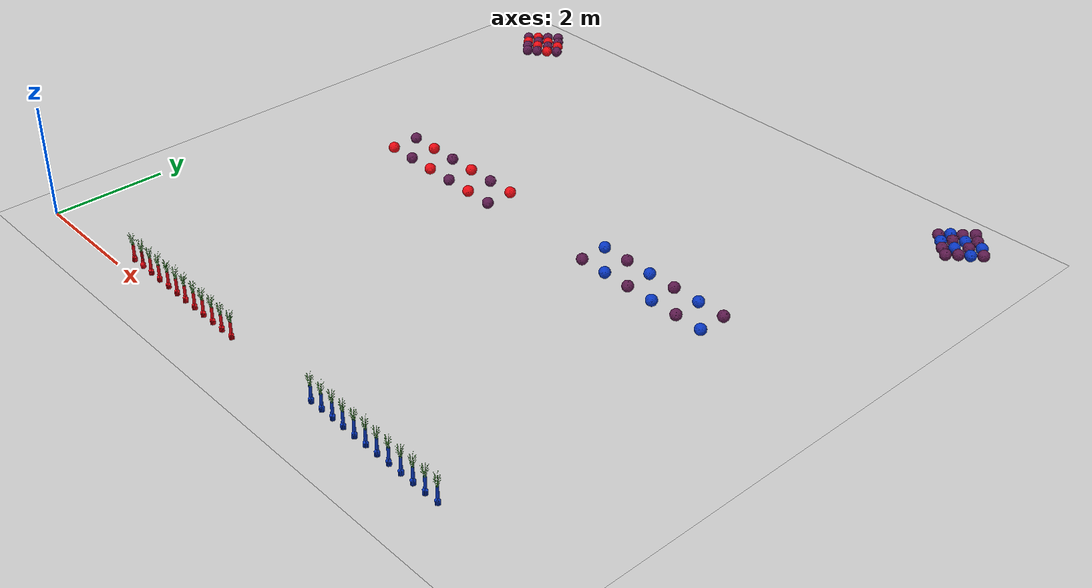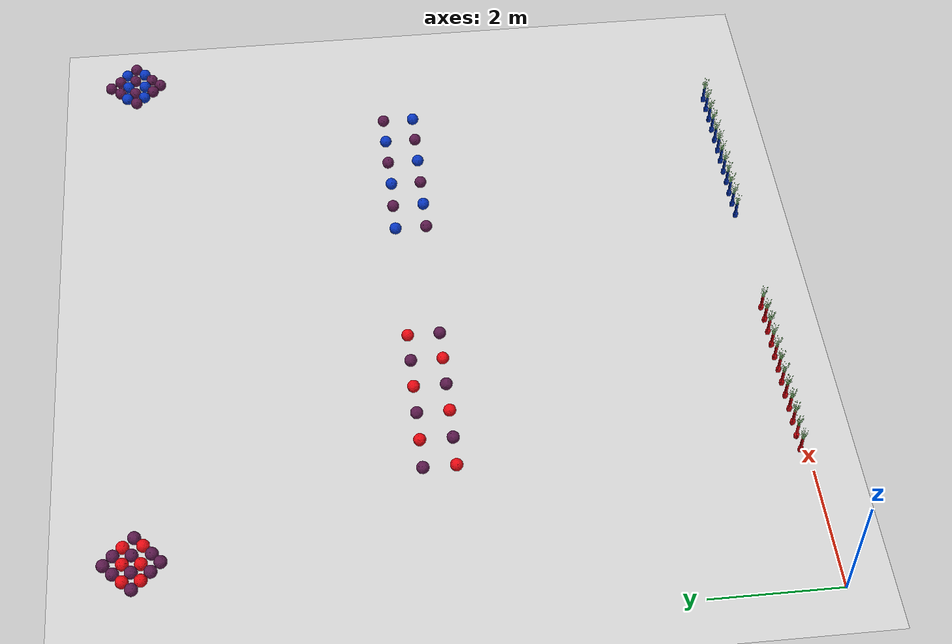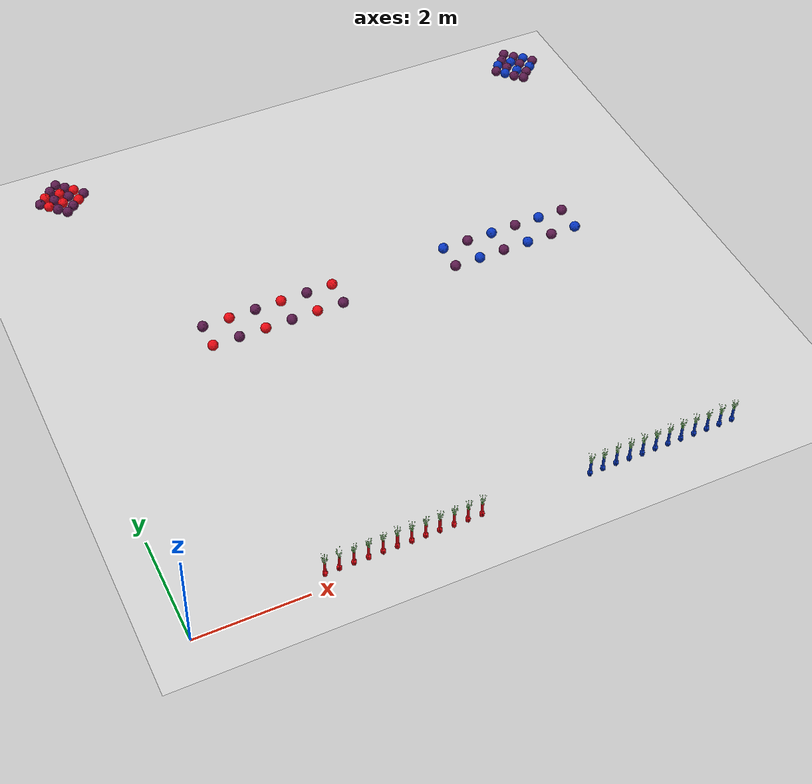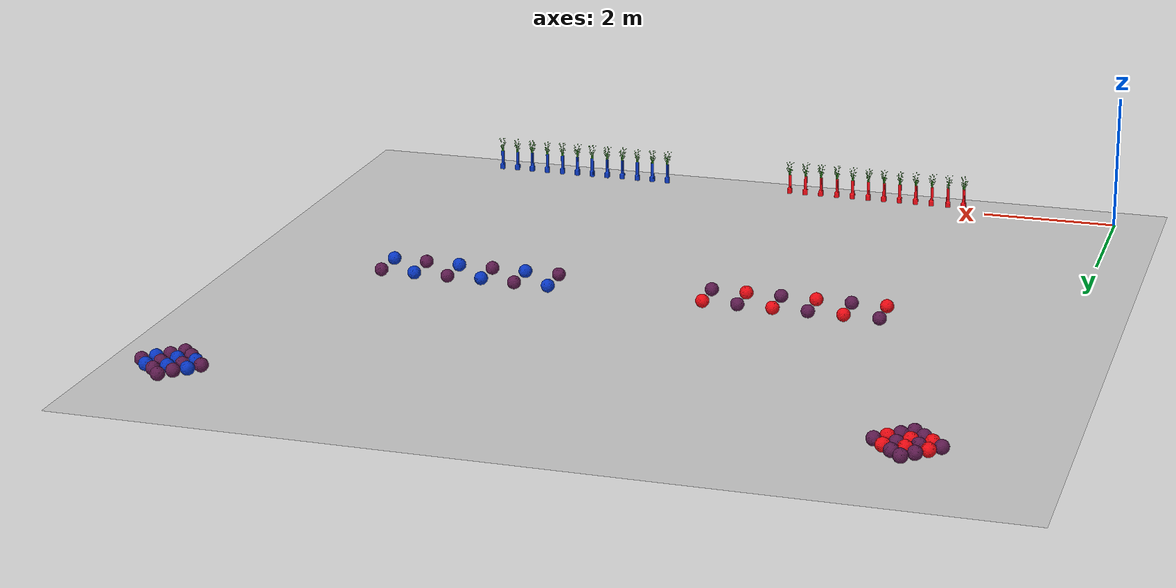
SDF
<sdf version="1.7">
 <world name="default">
  <light name="sun" type="directional">
   <pose>0 0 10 0 -0 0</pose>
   <diffuse>0.8 0.8 0.8 1</diffuse>
   <specular>0.2 0.2 0.2 1</specular>
   <attenuation>
    <range>1000</range>
    <constant>0.9</constant>
    <linear>0.01</linear>
    <quadratic>0.001</quadratic>
   </attenuation>
   <direction>-0.5 0.1 -0.9</direction>
   <spot><inner_angle>0</inner_angle><outer_angle>0</outer_angle><falloff>0</falloff></spot>
  </light>
  <model name="ground_plane">
   <static>1</static>
   <link name="link">
    <collision name="collision">
     <geometry><plane><normal>0 0 1</normal><size>100 100</size></plane></geometry>
     <surface>
      <contact><collide_bitmask>65535</collide_bitmask></contact>
      <friction><ode><mu>100</mu><mu2>50</mu2></ode></friction>
     </surface>
    </collision>
    <visual name="visual">
     <cast_shadows>0</cast_shadows>
     <geometry><plane><normal>0 0 1</normal><size>100 100</size></plane></geometry>
     <material>
      <script><uri>file://media/materials/scripts/gazebo.material</uri><name>Gazebo/Grey</name></script>
     </material>
    </visual>
   </link>
  </model>
  <gravity>0 0 -9.8</gravity>
  <magnetic_field>6e-06 2.3e-05 -4.2e-05</magnetic_field>
  <atmosphere type="adiabatic"/>
  <physics type="ode">
   <max_step_size>0.001</max_step_size>
   <real_time_factor>1</real_time_factor>
   <real_time_update_rate>1000</real_time_update_rate>
  </physics>
  <scene><ambient>0.4 0.4 0.4 1</ambient><background>0.7 0.7 0.7 1</background><shadows>1</shadows></scene>
  <audio><device>default</device></audio>
  <spherical_coordinates>
   <surface_model>EARTH_WGS84</surface_model>
   <latitude_deg>0</latitude_deg>
   <longitude_deg>0</longitude_deg>
   <elevation>0</elevation>
   <heading_deg>0</heading_deg>
  </spherical_coordinates>
  <model name="seed_red">
   <link name="link_1">
    <inertial>
     <mass>1</mass>
     <inertia>
      <ixx>0.166667</ixx>
      <ixy>0</ixy>
      <ixz>0</ixz>
      <iyy>0.166667</iyy>
      <iyz>0</iyz>
      <izz>0.166667</izz>
     </inertia>
    </inertial>
    <visual name="visual">
     <geometry>
      <mesh><uri>/home/entity014/abu2024_ws/src/abu_description/worlds/seed_red.dae</uri><scale>1 1 1</scale></mesh>
     </geometry>
    </visual>
    <collision name="collision">
     <geometry>
      <mesh><uri>/home/entity014/abu2024_ws/src/abu_description/worlds/seed_red.dae</uri><scale>1 1 1</scale></mesh>
     </geometry>
     <surface>
      <friction>
       <ode><mu>1</mu><mu2>1</mu2><fdir1>0 0 0</fdir1><slip1>0</slip1><slip2>0</slip2></ode>
       <torsional>
        <coefficient>1</coefficient>
        <patch_radius>0</patch_radius>
        <surface_radius>0</surface_radius>
        <use_patch_radius>1</use_patch_radius>
        <ode><slip>0</slip></ode>
       </torsional>
      </friction>
      <bounce><restitution_coefficient>0</restitution_coefficient><threshold>1e+06</threshold></bounce>
      <contact>
       <collide_without_contact>0</collide_without_contact>
       <collide_without_contact_bitmask>1</collide_without_contact_bitmask>
       <collide_bitmask>1</collide_bitmask>
       <ode>
        <soft_cfm>0</soft_cfm>
        <soft_erp>0.2</soft_erp>
        <kp>1e+13</kp>
        <kd>1</kd>
        <max_vel>0.01</max_vel>
        <min_depth>0</min_depth>
       </ode>
       <bullet>
        <split_impulse>1</split_impulse>
        <split_impulse_penetration_threshold>-0.01</split_impulse_penetration_threshold>
        <soft_cfm>0</soft_cfm>
        <soft_erp>0.2</soft_erp>
        <kp>1e+13</kp>
        <kd>1</kd>
       </bullet>
      </contact>
     </surface>
    </collision>
   </link>
   <static>0</static>
   <pose>2.30597 0.160398 0.24437 -1.2e-05 1e-06 -0.006202</pose>
  </model>
  <model name="seed_red_0">
   <link name="link_1">
    <inertial>
     <mass>1</mass>
     <inertia>
      <ixx>0.166667</ixx>
      <ixy>0</ixy>
      <ixz>0</ixz>
      <iyy>0.166667</iyy>
      <iyz>0</iyz>
      <izz>0.166667</izz>
     </inertia>
    </inertial>
    <visual name="visual">
     <geometry>
      <mesh><uri>/home/entity014/abu2024_ws/src/abu_description/worlds/seed_red.dae</uri><scale>1 1 1</scale></mesh>
     </geometry>
    </visual>
    <collision name="collision">
     <geometry>
      <mesh><uri>/home/entity014/abu2024_ws/src/abu_description/worlds/seed_red.dae</uri><scale>1 1 1</scale></mesh>
     </geometry>
     <surface>
      <friction>
       <ode><mu>1</mu><mu2>1</mu2><fdir1>0 0 0</fdir1><slip1>0</slip1><slip2>0</slip2></ode>
       <torsional>
        <coefficient>1</coefficient>
        <patch_radius>0</patch_radius>
        <surface_radius>0</surface_radius>
        <use_patch_radius>1</use_patch_radius>
        <ode><slip>0</slip></ode>
       </torsional>
      </friction>
      <bounce><restitution_coefficient>0</restitution_coefficient><threshold>1e+06</threshold></bounce>
      <contact>
       <collide_without_contact>0</collide_without_contact>
       <collide_without_contact_bitmask>1</collide_without_contact_bitmask>
       <collide_bitmask>1</collide_bitmask>
       <ode>
        <soft_cfm>0</soft_cfm>
        <soft_erp>0.2</soft_erp>
        <kp>1e+13</kp>
        <kd>1</kd>
        <max_vel>0.01</max_vel>
        <min_depth>0</min_depth>
       </ode>
       <bullet>
        <split_impulse>1</split_impulse>
        <split_impulse_penetration_threshold>-0.01</split_impulse_penetration_threshold>
        <soft_cfm>0</soft_cfm>
        <soft_erp>0.2</soft_erp>
        <kp>1e+13</kp>
        <kd>1</kd>
       </bullet>
      </contact>
     </surface>
    </collision>
   </link>
   <static>0</static>
   <pose>2.55212 0.166304 0.24458 0.005705 0.001673 -1.20475</pose>
  </model>
  <model name="seed_red_1">
   <link name="link_1">
    <inertial>
     <mass>1</mass>
     <inertia>
      <ixx>0.166667</ixx>
      <ixy>0</ixy>
      <ixz>0</ixz>
      <iyy>0.166667</iyy>
      <iyz>0</iyz>
      <izz>0.166667</izz>
     </inertia>
    </inertial>
    <visual name="visual">
     <geometry>
      <mesh><uri>/home/entity014/abu2024_ws/src/abu_description/worlds/seed_red.dae</uri><scale>1 1 1</scale></mesh>
     </geometry>
    </visual>
    <collision name="collision">
     <geometry>
      <mesh><uri>/home/entity014/abu2024_ws/src/abu_description/worlds/seed_red.dae</uri><scale>1 1 1</scale></mesh>
     </geometry>
     <surface>
      <friction>
       <ode><mu>1</mu><mu2>1</mu2><fdir1>0 0 0</fdir1><slip1>0</slip1><slip2>0</slip2></ode>
       <torsional>
        <coefficient>1</coefficient>
        <patch_radius>0</patch_radius>
        <surface_radius>0</surface_radius>
        <use_patch_radius>1</use_patch_radius>
        <ode><slip>0</slip></ode>
       </torsional>
      </friction>
      <bounce><restitution_coefficient>0</restitution_coefficient><threshold>1e+06</threshold></bounce>
      <contact>
       <collide_without_contact>0</collide_without_contact>
       <collide_without_contact_bitmask>1</collide_without_contact_bitmask>
       <collide_bitmask>1</collide_bitmask>
       <ode>
        <soft_cfm>0</soft_cfm>
        <soft_erp>0.2</soft_erp>
        <kp>1e+13</kp>
        <kd>1</kd>
        <max_vel>0.01</max_vel>
        <min_depth>0</min_depth>
       </ode>
       <bullet>
        <split_impulse>1</split_impulse>
        <split_impulse_penetration_threshold>-0.01</split_impulse_penetration_threshold>
        <soft_cfm>0</soft_cfm>
        <soft_erp>0.2</soft_erp>
        <kp>1e+13</kp>
        <kd>1</kd>
       </bullet>
      </contact>
     </surface>
    </collision>
   </link>
   <static>0</static>
   <pose>2.80489 0.163481 0.24436 -6e-06 -3e-06 0.181877</pose>
  </model>
  <model name="seed_red_2">
   <link name="link_1">
    <inertial>
     <mass>1</mass>
     <inertia>
      <ixx>0.166667</ixx>
      <ixy>0</ixy>
      <ixz>0</ixz>
      <iyy>0.166667</iyy>
      <iyz>0</iyz>
      <izz>0.166667</izz>
     </inertia>
    </inertial>
    <visual name="visual">
     <geometry>
      <mesh><uri>/home/entity014/abu2024_ws/src/abu_description/worlds/seed_red.dae</uri><scale>1 1 1</scale></mesh>
     </geometry>
    </visual>
    <collision name="collision">
     <geometry>
      <mesh><uri>/home/entity014/abu2024_ws/src/abu_description/worlds/seed_red.dae</uri><scale>1 1 1</scale></mesh>
     </geometry>
     <surface>
      <friction>
       <ode><mu>1</mu><mu2>1</mu2><fdir1>0 0 0</fdir1><slip1>0</slip1><slip2>0</slip2></ode>
       <torsional>
        <coefficient>1</coefficient>
        <patch_radius>0</patch_radius>
        <surface_radius>0</surface_radius>
        <use_patch_radius>1</use_patch_radius>
        <ode><slip>0</slip></ode>
       </torsional>
      </friction>
      <bounce><restitution_coefficient>0</restitution_coefficient><threshold>1e+06</threshold></bounce>
      <contact>
       <collide_without_contact>0</collide_without_contact>
       <collide_without_contact_bitmask>1</collide_without_contact_bitmask>
       <collide_bitmask>1</collide_bitmask>
       <ode>
        <soft_cfm>0</soft_cfm>
        <soft_erp>0.2</soft_erp>
        <kp>1e+13</kp>
        <kd>1</kd>
        <max_vel>0.01</max_vel>
        <min_depth>0</min_depth>
       </ode>
       <bullet>
        <split_impulse>1</split_impulse>
        <split_impulse_penetration_threshold>-0.01</split_impulse_penetration_threshold>
        <soft_cfm>0</soft_cfm>
        <soft_erp>0.2</soft_erp>
        <kp>1e+13</kp>
        <kd>1</kd>
       </bullet>
      </contact>
     </surface>
    </collision>
   </link>
   <static>0</static>
   <pose>3.05658 0.160245 0.244369 8e-06 -0 0.026436</pose>
  </model>
  <model name="seed_red_3">
   <link name="link_1">
    <inertial>
     <mass>1</mass>
     <inertia>
      <ixx>0.166667</ixx>
      <ixy>0</ixy>
      <ixz>0</ixz>
      <iyy>0.166667</iyy>
      <iyz>0</iyz>
      <izz>0.166667</izz>
     </inertia>
    </inertial>
    <visual name="visual">
     <geometry>
      <mesh><uri>/home/entity014/abu2024_ws/src/abu_description/worlds/seed_red.dae</uri><scale>1 1 1</scale></mesh>
     </geometry>
    </visual>
    <collision name="collision">
     <geometry>
      <mesh><uri>/home/entity014/abu2024_ws/src/abu_description/worlds/seed_red.dae</uri><scale>1 1 1</scale></mesh>
     </geometry>
     <surface>
      <friction>
       <ode><mu>1</mu><mu2>1</mu2><fdir1>0 0 0</fdir1><slip1>0</slip1><slip2>0</slip2></ode>
       <torsional>
        <coefficient>1</coefficient>
        <patch_radius>0</patch_radius>
        <surface_radius>0</surface_radius>
        <use_patch_radius>1</use_patch_radius>
        <ode><slip>0</slip></ode>
       </torsional>
      </friction>
      <bounce><restitution_coefficient>0</restitution_coefficient><threshold>1e+06</threshold></bounce>
      <contact>
       <collide_without_contact>0</collide_without_contact>
       <collide_without_contact_bitmask>1</collide_without_contact_bitmask>
       <collide_bitmask>1</collide_bitmask>
       <ode>
        <soft_cfm>0</soft_cfm>
        <soft_erp>0.2</soft_erp>
        <kp>1e+13</kp>
        <kd>1</kd>
        <max_vel>0.01</max_vel>
        <min_depth>0</min_depth>
       </ode>
       <bullet>
        <split_impulse>1</split_impulse>
        <split_impulse_penetration_threshold>-0.01</split_impulse_penetration_threshold>
        <soft_cfm>0</soft_cfm>
        <soft_erp>0.2</soft_erp>
        <kp>1e+13</kp>
        <kd>1</kd>
       </bullet>
      </contact>
     </surface>
    </collision>
   </link>
   <static>0</static>
   <pose>3.30914 0.16565 0.24436 9e-06 -1e-06 -0.000431</pose>
  </model>
  <model name="seed_red_4">
   <link name="link_1">
    <inertial>
     <mass>1</mass>
     <inertia>
      <ixx>0.166667</ixx>
      <ixy>0</ixy>
      <ixz>0</ixz>
      <iyy>0.166667</iyy>
      <iyz>0</iyz>
      <izz>0.166667</izz>
     </inertia>
    </inertial>
    <visual name="visual">
     <geometry>
      <mesh><uri>/home/entity014/abu2024_ws/src/abu_description/worlds/seed_red.dae</uri><scale>1 1 1</scale></mesh>
     </geometry>
    </visual>
    <collision name="collision">
     <geometry>
      <mesh><uri>/home/entity014/abu2024_ws/src/abu_description/worlds/seed_red.dae</uri><scale>1 1 1</scale></mesh>
     </geometry>
     <surface>
      <friction>
       <ode><mu>1</mu><mu2>1</mu2><fdir1>0 0 0</fdir1><slip1>0</slip1><slip2>0</slip2></ode>
       <torsional>
        <coefficient>1</coefficient>
        <patch_radius>0</patch_radius>
        <surface_radius>0</surface_radius>
        <use_patch_radius>1</use_patch_radius>
        <ode><slip>0</slip></ode>
       </torsional>
      </friction>
      <bounce><restitution_coefficient>0</restitution_coefficient><threshold>1e+06</threshold></bounce>
      <contact>
       <collide_without_contact>0</collide_without_contact>
       <collide_without_contact_bitmask>1</collide_without_contact_bitmask>
       <collide_bitmask>1</collide_bitmask>
       <ode>
        <soft_cfm>0</soft_cfm>
        <soft_erp>0.2</soft_erp>
        <kp>1e+13</kp>
        <kd>1</kd>
        <max_vel>0.01</max_vel>
        <min_depth>0</min_depth>
       </ode>
       <bullet>
        <split_impulse>1</split_impulse>
        <split_impulse_penetration_threshold>-0.01</split_impulse_penetration_threshold>
        <soft_cfm>0</soft_cfm>
        <soft_erp>0.2</soft_erp>
        <kp>1e+13</kp>
        <kd>1</kd>
       </bullet>
      </contact>
     </surface>
    </collision>
   </link>
   <static>0</static>
   <pose>3.55706 0.165017 0.244359 1e-06 1e-06 0.007021</pose>
  </model>
  <model name="seed_red_5">
   <link name="link_1">
    <inertial>
     <mass>1</mass>
     <inertia>
      <ixx>0.166667</ixx>
      <ixy>0</ixy>
      <ixz>0</ixz>
      <iyy>0.166667</iyy>
      <iyz>0</iyz>
      <izz>0.166667</izz>
     </inertia>
    </inertial>
    <visual name="visual">
     <geometry>
      <mesh><uri>/home/entity014/abu2024_ws/src/abu_description/worlds/seed_red.dae</uri><scale>1 1 1</scale></mesh>
     </geometry>
    </visual>
    <collision name="collision">
     <geometry>
      <mesh><uri>/home/entity014/abu2024_ws/src/abu_description/worlds/seed_red.dae</uri><scale>1 1 1</scale></mesh>
     </geometry>
     <surface>
      <friction>
       <ode><mu>1</mu><mu2>1</mu2><fdir1>0 0 0</fdir1><slip1>0</slip1><slip2>0</slip2></ode>
       <torsional>
        <coefficient>1</coefficient>
        <patch_radius>0</patch_radius>
        <surface_radius>0</surface_radius>
        <use_patch_radius>1</use_patch_radius>
        <ode><slip>0</slip></ode>
       </torsional>
      </friction>
      <bounce><restitution_coefficient>0</restitution_coefficient><threshold>1e+06</threshold></bounce>
      <contact>
       <collide_without_contact>0</collide_without_contact>
       <collide_without_contact_bitmask>1</collide_without_contact_bitmask>
       <collide_bitmask>1</collide_bitmask>
       <ode>
        <soft_cfm>0</soft_cfm>
        <soft_erp>0.2</soft_erp>
        <kp>1e+13</kp>
        <kd>1</kd>
        <max_vel>0.01</max_vel>
        <min_depth>0</min_depth>
       </ode>
       <bullet>
        <split_impulse>1</split_impulse>
        <split_impulse_penetration_threshold>-0.01</split_impulse_penetration_threshold>
        <soft_cfm>0</soft_cfm>
        <soft_erp>0.2</soft_erp>
        <kp>1e+13</kp>
        <kd>1</kd>
       </bullet>
      </contact>
     </surface>
    </collision>
   </link>
   <static>0</static>
   <pose>3.80696 0.160767 0.24437 8e-06 -9e-06 -0.002747</pose>
  </model>
  <model name="seed_red_6">
   <link name="link_1">
    <inertial>
     <mass>1</mass>
     <inertia>
      <ixx>0.166667</ixx>
      <ixy>0</ixy>
      <ixz>0</ixz>
      <iyy>0.166667</iyy>
      <iyz>0</iyz>
      <izz>0.166667</izz>
     </inertia>
    </inertial>
    <visual name="visual">
     <geometry>
      <mesh><uri>/home/entity014/abu2024_ws/src/abu_description/worlds/seed_red.dae</uri><scale>1 1 1</scale></mesh>
     </geometry>
    </visual>
    <collision name="collision">
     <geometry>
      <mesh><uri>/home/entity014/abu2024_ws/src/abu_description/worlds/seed_red.dae</uri><scale>1 1 1</scale></mesh>
     </geometry>
     <surface>
      <friction>
       <ode><mu>1</mu><mu2>1</mu2><fdir1>0 0 0</fdir1><slip1>0</slip1><slip2>0</slip2></ode>
       <torsional>
        <coefficient>1</coefficient>
        <patch_radius>0</patch_radius>
        <surface_radius>0</surface_radius>
        <use_patch_radius>1</use_patch_radius>
        <ode><slip>0</slip></ode>
       </torsional>
      </friction>
      <bounce><restitution_coefficient>0</restitution_coefficient><threshold>1e+06</threshold></bounce>
      <contact>
       <collide_without_contact>0</collide_without_contact>
       <collide_without_contact_bitmask>1</collide_without_contact_bitmask>
       <collide_bitmask>1</collide_bitmask>
       <ode>
        <soft_cfm>0</soft_cfm>
        <soft_erp>0.2</soft_erp>
        <kp>1e+13</kp>
        <kd>1</kd>
        <max_vel>0.01</max_vel>
        <min_depth>0</min_depth>
       </ode>
       <bullet>
        <split_impulse>1</split_impulse>
        <split_impulse_penetration_threshold>-0.01</split_impulse_penetration_threshold>
        <soft_cfm>0</soft_cfm>
        <soft_erp>0.2</soft_erp>
        <kp>1e+13</kp>
        <kd>1</kd>
       </bullet>
      </contact>
     </surface>
    </collision>
   </link>
   <static>0</static>
   <pose>4.0561 0.163957 0.244369 -2e-06 -2e-06 -0.032654</pose>
  </model>
  <model name="seed_red_7">
   <link name="link_1">
    <inertial>
     <mass>1</mass>
     <inertia>
      <ixx>0.166667</ixx>
      <ixy>0</ixy>
      <ixz>0</ixz>
      <iyy>0.166667</iyy>
      <iyz>0</iyz>
      <izz>0.166667</izz>
     </inertia>
    </inertial>
    <visual name="visual">
     <geometry>
      <mesh><uri>/home/entity014/abu2024_ws/src/abu_description/worlds/seed_red.dae</uri><scale>1 1 1</scale></mesh>
     </geometry>
    </visual>
    <collision name="collision">
     <geometry>
      <mesh><uri>/home/entity014/abu2024_ws/src/abu_description/worlds/seed_red.dae</uri><scale>1 1 1</scale></mesh>
     </geometry>
     <surface>
      <friction>
       <ode><mu>1</mu><mu2>1</mu2><fdir1>0 0 0</fdir1><slip1>0</slip1><slip2>0</slip2></ode>
       <torsional>
        <coefficient>1</coefficient>
        <patch_radius>0</patch_radius>
        <surface_radius>0</surface_radius>
        <use_patch_radius>1</use_patch_radius>
        <ode><slip>0</slip></ode>
       </torsional>
      </friction>
      <bounce><restitution_coefficient>0</restitution_coefficient><threshold>1e+06</threshold></bounce>
      <contact>
       <collide_without_contact>0</collide_without_contact>
       <collide_without_contact_bitmask>1</collide_without_contact_bitmask>
       <collide_bitmask>1</collide_bitmask>
       <ode>
        <soft_cfm>0</soft_cfm>
        <soft_erp>0.2</soft_erp>
        <kp>1e+13</kp>
        <kd>1</kd>
        <max_vel>0.01</max_vel>
        <min_depth>0</min_depth>
       </ode>
       <bullet>
        <split_impulse>1</split_impulse>
        <split_impulse_penetration_threshold>-0.01</split_impulse_penetration_threshold>
        <soft_cfm>0</soft_cfm>
        <soft_erp>0.2</soft_erp>
        <kp>1e+13</kp>
        <kd>1</kd>
       </bullet>
      </contact>
     </surface>
    </collision>
   </link>
   <static>0</static>
   <pose>4.30494 0.160938 0.244369 1e-06 0 -0.020629</pose>
  </model>
  <model name="seed_red_8">
   <link name="link_1">
    <inertial>
     <mass>1</mass>
     <inertia>
      <ixx>0.166667</ixx>
      <ixy>0</ixy>
      <ixz>0</ixz>
      <iyy>0.166667</iyy>
      <iyz>0</iyz>
      <izz>0.166667</izz>
     </inertia>
    </inertial>
    <visual name="visual">
     <geometry>
      <mesh><uri>/home/entity014/abu2024_ws/src/abu_description/worlds/seed_red.dae</uri><scale>1 1 1</scale></mesh>
     </geometry>
    </visual>
    <collision name="collision">
     <geometry>
      <mesh><uri>/home/entity014/abu2024_ws/src/abu_description/worlds/seed_red.dae</uri><scale>1 1 1</scale></mesh>
     </geometry>
     <surface>
      <friction>
       <ode><mu>1</mu><mu2>1</mu2><fdir1>0 0 0</fdir1><slip1>0</slip1><slip2>0</slip2></ode>
       <torsional>
        <coefficient>1</coefficient>
        <patch_radius>0</patch_radius>
        <surface_radius>0</surface_radius>
        <use_patch_radius>1</use_patch_radius>
        <ode><slip>0</slip></ode>
       </torsional>
      </friction>
      <bounce><restitution_coefficient>0</restitution_coefficient><threshold>1e+06</threshold></bounce>
      <contact>
       <collide_without_contact>0</collide_without_contact>
       <collide_without_contact_bitmask>1</collide_without_contact_bitmask>
       <collide_bitmask>1</collide_bitmask>
       <ode>
        <soft_cfm>0</soft_cfm>
        <soft_erp>0.2</soft_erp>
        <kp>1e+13</kp>
        <kd>1</kd>
        <max_vel>0.01</max_vel>
        <min_depth>0</min_depth>
       </ode>
       <bullet>
        <split_impulse>1</split_impulse>
        <split_impulse_penetration_threshold>-0.01</split_impulse_penetration_threshold>
        <soft_cfm>0</soft_cfm>
        <soft_erp>0.2</soft_erp>
        <kp>1e+13</kp>
        <kd>1</kd>
       </bullet>
      </contact>
     </surface>
    </collision>
   </link>
   <static>0</static>
   <pose>4.5602 0.162002 0.244369 -4e-06 -1e-06 0.000196</pose>
  </model>
  <model name="seed_red_9">
   <link name="link_1">
    <inertial>
     <mass>1</mass>
     <inertia>
      <ixx>0.166667</ixx>
      <ixy>0</ixy>
      <ixz>0</ixz>
      <iyy>0.166667</iyy>
      <iyz>0</iyz>
      <izz>0.166667</izz>
     </inertia>
    </inertial>
    <visual name="visual">
     <geometry>
      <mesh><uri>/home/entity014/abu2024_ws/src/abu_description/worlds/seed_red.dae</uri><scale>1 1 1</scale></mesh>
     </geometry>
    </visual>
    <collision name="collision">
     <geometry>
      <mesh><uri>/home/entity014/abu2024_ws/src/abu_description/worlds/seed_red.dae</uri><scale>1 1 1</scale></mesh>
     </geometry>
     <surface>
      <friction>
       <ode><mu>1</mu><mu2>1</mu2><fdir1>0 0 0</fdir1><slip1>0</slip1><slip2>0</slip2></ode>
       <torsional>
        <coefficient>1</coefficient>
        <patch_radius>0</patch_radius>
        <surface_radius>0</surface_radius>
        <use_patch_radius>1</use_patch_radius>
        <ode><slip>0</slip></ode>
       </torsional>
      </friction>
      <bounce><restitution_coefficient>0</restitution_coefficient><threshold>1e+06</threshold></bounce>
      <contact>
       <collide_without_contact>0</collide_without_contact>
       <collide_without_contact_bitmask>1</collide_without_contact_bitmask>
       <collide_bitmask>1</collide_bitmask>
       <ode>
        <soft_cfm>0</soft_cfm>
        <soft_erp>0.2</soft_erp>
        <kp>1e+13</kp>
        <kd>1</kd>
        <max_vel>0.01</max_vel>
        <min_depth>0</min_depth>
       </ode>
       <bullet>
        <split_impulse>1</split_impulse>
        <split_impulse_penetration_threshold>-0.01</split_impulse_penetration_threshold>
        <soft_cfm>0</soft_cfm>
        <soft_erp>0.2</soft_erp>
        <kp>1e+13</kp>
        <kd>1</kd>
       </bullet>
      </contact>
     </surface>
    </collision>
   </link>
   <static>0</static>
   <pose>4.80888 0.160135 0.24436 -4e-06 -0 0.116225</pose>
  </model>
  <model name="seed_red_10">
   <link name="link_1">
    <inertial>
     <mass>1</mass>
     <inertia>
      <ixx>0.166667</ixx>
      <ixy>0</ixy>
      <ixz>0</ixz>
      <iyy>0.166667</iyy>
      <iyz>0</iyz>
      <izz>0.166667</izz>
     </inertia>
    </inertial>
    <visual name="visual">
     <geometry>
      <mesh><uri>/home/entity014/abu2024_ws/src/abu_description/worlds/seed_red.dae</uri><scale>1 1 1</scale></mesh>
     </geometry>
    </visual>
    <collision name="collision">
     <geometry>
      <mesh><uri>/home/entity014/abu2024_ws/src/abu_description/worlds/seed_red.dae</uri><scale>1 1 1</scale></mesh>
     </geometry>
     <surface>
      <friction>
       <ode><mu>1</mu><mu2>1</mu2><fdir1>0 0 0</fdir1><slip1>0</slip1><slip2>0</slip2></ode>
       <torsional>
        <coefficient>1</coefficient>
        <patch_radius>0</patch_radius>
        <surface_radius>0</surface_radius>
        <use_patch_radius>1</use_patch_radius>
        <ode><slip>0</slip></ode>
       </torsional>
      </friction>
      <bounce><restitution_coefficient>0</restitution_coefficient><threshold>1e+06</threshold></bounce>
      <contact>
       <collide_without_contact>0</collide_without_contact>
       <collide_without_contact_bitmask>1</collide_without_contact_bitmask>
       <collide_bitmask>1</collide_bitmask>
       <ode>
        <soft_cfm>0</soft_cfm>
        <soft_erp>0.2</soft_erp>
        <kp>1e+13</kp>
        <kd>1</kd>
        <max_vel>0.01</max_vel>
        <min_depth>0</min_depth>
       </ode>
       <bullet>
        <split_impulse>1</split_impulse>
        <split_impulse_penetration_threshold>-0.01</split_impulse_penetration_threshold>
        <soft_cfm>0</soft_cfm>
        <soft_erp>0.2</soft_erp>
        <kp>1e+13</kp>
        <kd>1</kd>
       </bullet>
      </contact>
     </surface>
    </collision>
   </link>
   <static>0</static>
   <pose>5.06177 0.161648 0.24436 -2e-06 9e-06 0.173465</pose>
  </model>
  <model name="seed_blue">
   <link name="link_1">
    <inertial>
     <mass>1</mass>
     <inertia>
      <ixx>0.166667</ixx>
      <ixy>0</ixy>
      <ixz>0</ixz>
      <iyy>0.166667</iyy>
      <iyz>0</iyz>
      <izz>0.166667</izz>
     </inertia>
    </inertial>
    <visual name="visual">
     <geometry>
      <mesh>
       <uri>/home/entity014/abu2024_ws/src/abu_description/worlds/seed_blue.dae</uri>
       <scale>1 1 1</scale>
      </mesh>
     </geometry>
    </visual>
    <collision name="collision">
     <geometry>
      <mesh>
       <uri>/home/entity014/abu2024_ws/src/abu_description/worlds/seed_blue.dae</uri>
       <scale>1 1 1</scale>
      </mesh>
     </geometry>
     <surface>
      <friction>
       <ode><mu>1</mu><mu2>1</mu2><fdir1>0 0 0</fdir1><slip1>0</slip1><slip2>0</slip2></ode>
       <torsional>
        <coefficient>1</coefficient>
        <patch_radius>0</patch_radius>
        <surface_radius>0</surface_radius>
        <use_patch_radius>1</use_patch_radius>
        <ode><slip>0</slip></ode>
       </torsional>
      </friction>
      <bounce><restitution_coefficient>0</restitution_coefficient><threshold>1e+06</threshold></bounce>
      <contact>
       <collide_without_contact>0</collide_without_contact>
       <collide_without_contact_bitmask>1</collide_without_contact_bitmask>
       <collide_bitmask>1</collide_bitmask>
       <ode>
        <soft_cfm>0</soft_cfm>
        <soft_erp>0.2</soft_erp>
        <kp>1e+13</kp>
        <kd>1</kd>
        <max_vel>0.01</max_vel>
        <min_depth>0</min_depth>
       </ode>
       <bullet>
        <split_impulse>1</split_impulse>
        <split_impulse_penetration_threshold>-0.01</split_impulse_penetration_threshold>
        <soft_cfm>0</soft_cfm>
        <soft_erp>0.2</soft_erp>
        <kp>1e+13</kp>
        <kd>1</kd>
       </bullet>
      </contact>
     </surface>
    </collision>
   </link>
   <static>0</static>
   <pose>7.05811 0.163128 0.24436 1.2e-05 -6e-06 0.000145</pose>
  </model>
  <model name="seed_blue_0">
   <link name="link_1">
    <inertial>
     <mass>1</mass>
     <inertia>
      <ixx>0.166667</ixx>
      <ixy>0</ixy>
      <ixz>0</ixz>
      <iyy>0.166667</iyy>
      <iyz>0</iyz>
      <izz>0.166667</izz>
     </inertia>
    </inertial>
    <visual name="visual">
     <geometry>
      <mesh>
       <uri>/home/entity014/abu2024_ws/src/abu_description/worlds/seed_blue.dae</uri>
       <scale>1 1 1</scale>
      </mesh>
     </geometry>
    </visual>
    <collision name="collision">
     <geometry>
      <mesh>
       <uri>/home/entity014/abu2024_ws/src/abu_description/worlds/seed_blue.dae</uri>
       <scale>1 1 1</scale>
      </mesh>
     </geometry>
     <surface>
      <friction>
       <ode><mu>1</mu><mu2>1</mu2><fdir1>0 0 0</fdir1><slip1>0</slip1><slip2>0</slip2></ode>
       <torsional>
        <coefficient>1</coefficient>
        <patch_radius>0</patch_radius>
        <surface_radius>0</surface_radius>
        <use_patch_radius>1</use_patch_radius>
        <ode><slip>0</slip></ode>
       </torsional>
      </friction>
      <bounce><restitution_coefficient>0</restitution_coefficient><threshold>1e+06</threshold></bounce>
      <contact>
       <collide_without_contact>0</collide_without_contact>
       <collide_without_contact_bitmask>1</collide_without_contact_bitmask>
       <collide_bitmask>1</collide_bitmask>
       <ode>
        <soft_cfm>0</soft_cfm>
        <soft_erp>0.2</soft_erp>
        <kp>1e+13</kp>
        <kd>1</kd>
        <max_vel>0.01</max_vel>
        <min_depth>0</min_depth>
       </ode>
       <bullet>
        <split_impulse>1</split_impulse>
        <split_impulse_penetration_threshold>-0.01</split_impulse_penetration_threshold>
        <soft_cfm>0</soft_cfm>
        <soft_erp>0.2</soft_erp>
        <kp>1e+13</kp>
        <kd>1</kd>
       </bullet>
      </contact>
     </surface>
    </collision>
   </link>
   <static>0</static>
   <pose>7.30361 0.167484 0.244369 3e-06 -3e-06 -0.016872</pose>
  </model>
  <model name="seed_blue_1">
   <link name="link_1">
    <inertial>
     <mass>1</mass>
     <inertia>
      <ixx>0.166667</ixx>
      <ixy>0</ixy>
      <ixz>0</ixz>
      <iyy>0.166667</iyy>
      <iyz>0</iyz>
      <izz>0.166667</izz>
     </inertia>
    </inertial>
    <visual name="visual">
     <geometry>
      <mesh>
       <uri>/home/entity014/abu2024_ws/src/abu_description/worlds/seed_blue.dae</uri>
       <scale>1 1 1</scale>
      </mesh>
     </geometry>
    </visual>
    <collision name="collision">
     <geometry>
      <mesh>
       <uri>/home/entity014/abu2024_ws/src/abu_description/worlds/seed_blue.dae</uri>
       <scale>1 1 1</scale>
      </mesh>
     </geometry>
     <surface>
      <friction>
       <ode><mu>1</mu><mu2>1</mu2><fdir1>0 0 0</fdir1><slip1>0</slip1><slip2>0</slip2></ode>
       <torsional>
        <coefficient>1</coefficient>
        <patch_radius>0</patch_radius>
        <surface_radius>0</surface_radius>
        <use_patch_radius>1</use_patch_radius>
        <ode><slip>0</slip></ode>
       </torsional>
      </friction>
      <bounce><restitution_coefficient>0</restitution_coefficient><threshold>1e+06</threshold></bounce>
      <contact>
       <collide_without_contact>0</collide_without_contact>
       <collide_without_contact_bitmask>1</collide_without_contact_bitmask>
       <collide_bitmask>1</collide_bitmask>
       <ode>
        <soft_cfm>0</soft_cfm>
        <soft_erp>0.2</soft_erp>
        <kp>1e+13</kp>
        <kd>1</kd>
        <max_vel>0.01</max_vel>
        <min_depth>0</min_depth>
       </ode>
       <bullet>
        <split_impulse>1</split_impulse>
        <split_impulse_penetration_threshold>-0.01</split_impulse_penetration_threshold>
        <soft_cfm>0</soft_cfm>
        <soft_erp>0.2</soft_erp>
        <kp>1e+13</kp>
        <kd>1</kd>
       </bullet>
      </contact>
     </surface>
    </collision>
   </link>
   <static>0</static>
   <pose>7.5539 0.168938 0.244359 -6e-06 1e-06 -7e-06</pose>
  </model>
  <model name="seed_blue_2">
   <link name="link_1">
    <inertial>
     <mass>1</mass>
     <inertia>
      <ixx>0.166667</ixx>
      <ixy>0</ixy>
      <ixz>0</ixz>
      <iyy>0.166667</iyy>
      <iyz>0</iyz>
      <izz>0.166667</izz>
     </inertia>
    </inertial>
    <visual name="visual">
     <geometry>
      <mesh>
       <uri>/home/entity014/abu2024_ws/src/abu_description/worlds/seed_blue.dae</uri>
       <scale>1 1 1</scale>
      </mesh>
     </geometry>
    </visual>
    <collision name="collision">
     <geometry>
      <mesh>
       <uri>/home/entity014/abu2024_ws/src/abu_description/worlds/seed_blue.dae</uri>
       <scale>1 1 1</scale>
      </mesh>
     </geometry>
     <surface>
      <friction>
       <ode><mu>1</mu><mu2>1</mu2><fdir1>0 0 0</fdir1><slip1>0</slip1><slip2>0</slip2></ode>
       <torsional>
        <coefficient>1</coefficient>
        <patch_radius>0</patch_radius>
        <surface_radius>0</surface_radius>
        <use_patch_radius>1</use_patch_radius>
        <ode><slip>0</slip></ode>
       </torsional>
      </friction>
      <bounce><restitution_coefficient>0</restitution_coefficient><threshold>1e+06</threshold></bounce>
      <contact>
       <collide_without_contact>0</collide_without_contact>
       <collide_without_contact_bitmask>1</collide_without_contact_bitmask>
       <collide_bitmask>1</collide_bitmask>
       <ode>
        <soft_cfm>0</soft_cfm>
        <soft_erp>0.2</soft_erp>
        <kp>1e+13</kp>
        <kd>1</kd>
        <max_vel>0.01</max_vel>
        <min_depth>0</min_depth>
       </ode>
       <bullet>
        <split_impulse>1</split_impulse>
        <split_impulse_penetration_threshold>-0.01</split_impulse_penetration_threshold>
        <soft_cfm>0</soft_cfm>
        <soft_erp>0.2</soft_erp>
        <kp>1e+13</kp>
        <kd>1</kd>
       </bullet>
      </contact>
     </surface>
    </collision>
   </link>
   <static>0</static>
   <pose>7.80373 0.163087 0.244369 4e-06 -2e-06 -0.00013</pose>
  </model>
  <model name="seed_blue_3">
   <link name="link_1">
    <inertial>
     <mass>1</mass>
     <inertia>
      <ixx>0.166667</ixx>
      <ixy>0</ixy>
      <ixz>0</ixz>
      <iyy>0.166667</iyy>
      <iyz>0</iyz>
      <izz>0.166667</izz>
     </inertia>
    </inertial>
    <visual name="visual">
     <geometry>
      <mesh>
       <uri>/home/entity014/abu2024_ws/src/abu_description/worlds/seed_blue.dae</uri>
       <scale>1 1 1</scale>
      </mesh>
     </geometry>
    </visual>
    <collision name="collision">
     <geometry>
      <mesh>
       <uri>/home/entity014/abu2024_ws/src/abu_description/worlds/seed_blue.dae</uri>
       <scale>1 1 1</scale>
      </mesh>
     </geometry>
     <surface>
      <friction>
       <ode><mu>1</mu><mu2>1</mu2><fdir1>0 0 0</fdir1><slip1>0</slip1><slip2>0</slip2></ode>
       <torsional>
        <coefficient>1</coefficient>
        <patch_radius>0</patch_radius>
        <surface_radius>0</surface_radius>
        <use_patch_radius>1</use_patch_radius>
        <ode><slip>0</slip></ode>
       </torsional>
      </friction>
      <bounce><restitution_coefficient>0</restitution_coefficient><threshold>1e+06</threshold></bounce>
      <contact>
       <collide_without_contact>0</collide_without_contact>
       <collide_without_contact_bitmask>1</collide_without_contact_bitmask>
       <collide_bitmask>1</collide_bitmask>
       <ode>
        <soft_cfm>0</soft_cfm>
        <soft_erp>0.2</soft_erp>
        <kp>1e+13</kp>
        <kd>1</kd>
        <max_vel>0.01</max_vel>
        <min_depth>0</min_depth>
       </ode>
       <bullet>
        <split_impulse>1</split_impulse>
        <split_impulse_penetration_threshold>-0.01</split_impulse_penetration_threshold>
        <soft_cfm>0</soft_cfm>
        <soft_erp>0.2</soft_erp>
        <kp>1e+13</kp>
        <kd>1</kd>
       </bullet>
      </contact>
     </surface>
    </collision>
   </link>
   <static>0</static>
   <pose>8.05521 0.164025 0.244369 5e-06 -1e-05 5.9e-05</pose>
  </model>
  <model name="seed_blue_4">
   <link name="link_1">
    <inertial>
     <mass>1</mass>
     <inertia>
      <ixx>0.166667</ixx>
      <ixy>0</ixy>
      <ixz>0</ixz>
      <iyy>0.166667</iyy>
      <iyz>0</iyz>
      <izz>0.166667</izz>
     </inertia>
    </inertial>
    <visual name="visual">
     <geometry>
      <mesh>
       <uri>/home/entity014/abu2024_ws/src/abu_description/worlds/seed_blue.dae</uri>
       <scale>1 1 1</scale>
      </mesh>
     </geometry>
    </visual>
    <collision name="collision">
     <geometry>
      <mesh>
       <uri>/home/entity014/abu2024_ws/src/abu_description/worlds/seed_blue.dae</uri>
       <scale>1 1 1</scale>
      </mesh>
     </geometry>
     <surface>
      <friction>
       <ode><mu>1</mu><mu2>1</mu2><fdir1>0 0 0</fdir1><slip1>0</slip1><slip2>0</slip2></ode>
       <torsional>
        <coefficient>1</coefficient>
        <patch_radius>0</patch_radius>
        <surface_radius>0</surface_radius>
        <use_patch_radius>1</use_patch_radius>
        <ode><slip>0</slip></ode>
       </torsional>
      </friction>
      <bounce><restitution_coefficient>0</restitution_coefficient><threshold>1e+06</threshold></bounce>
      <contact>
       <collide_without_contact>0</collide_without_contact>
       <collide_without_contact_bitmask>1</collide_without_contact_bitmask>
       <collide_bitmask>1</collide_bitmask>
       <ode>
        <soft_cfm>0</soft_cfm>
        <soft_erp>0.2</soft_erp>
        <kp>1e+13</kp>
        <kd>1</kd>
        <max_vel>0.01</max_vel>
        <min_depth>0</min_depth>
       </ode>
       <bullet>
        <split_impulse>1</split_impulse>
        <split_impulse_penetration_threshold>-0.01</split_impulse_penetration_threshold>
        <soft_cfm>0</soft_cfm>
        <soft_erp>0.2</soft_erp>
        <kp>1e+13</kp>
        <kd>1</kd>
       </bullet>
      </contact>
     </surface>
    </collision>
   </link>
   <static>0</static>
   <pose>8.30615 0.165431 0.244369 -2e-06 1e-06 -0.000607</pose>
  </model>
  <model name="seed_blue_5">
   <link name="link_1">
    <inertial>
     <mass>1</mass>
     <inertia>
      <ixx>0.166667</ixx>
      <ixy>0</ixy>
      <ixz>0</ixz>
      <iyy>0.166667</iyy>
      <iyz>0</iyz>
      <izz>0.166667</izz>
     </inertia>
    </inertial>
    <visual name="visual">
     <geometry>
      <mesh>
       <uri>/home/entity014/abu2024_ws/src/abu_description/worlds/seed_blue.dae</uri>
       <scale>1 1 1</scale>
      </mesh>
     </geometry>
    </visual>
    <collision name="collision">
     <geometry>
      <mesh>
       <uri>/home/entity014/abu2024_ws/src/abu_description/worlds/seed_blue.dae</uri>
       <scale>1 1 1</scale>
      </mesh>
     </geometry>
     <surface>
      <friction>
       <ode><mu>1</mu><mu2>1</mu2><fdir1>0 0 0</fdir1><slip1>0</slip1><slip2>0</slip2></ode>
       <torsional>
        <coefficient>1</coefficient>
        <patch_radius>0</patch_radius>
        <surface_radius>0</surface_radius>
        <use_patch_radius>1</use_patch_radius>
        <ode><slip>0</slip></ode>
       </torsional>
      </friction>
      <bounce><restitution_coefficient>0</restitution_coefficient><threshold>1e+06</threshold></bounce>
      <contact>
       <collide_without_contact>0</collide_without_contact>
       <collide_without_contact_bitmask>1</collide_without_contact_bitmask>
       <collide_bitmask>1</collide_bitmask>
       <ode>
        <soft_cfm>0</soft_cfm>
        <soft_erp>0.2</soft_erp>
        <kp>1e+13</kp>
        <kd>1</kd>
        <max_vel>0.01</max_vel>
        <min_depth>0</min_depth>
       </ode>
       <bullet>
        <split_impulse>1</split_impulse>
        <split_impulse_penetration_threshold>-0.01</split_impulse_penetration_threshold>
        <soft_cfm>0</soft_cfm>
        <soft_erp>0.2</soft_erp>
        <kp>1e+13</kp>
        <kd>1</kd>
       </bullet>
      </contact>
     </surface>
    </collision>
   </link>
   <static>0</static>
   <pose>8.5531 0.164073 0.244369 7e-06 1.2e-05 -5e-06</pose>
  </model>
  <model name="seed_blue_6">
   <link name="link_1">
    <inertial>
     <mass>1</mass>
     <inertia>
      <ixx>0.166667</ixx>
      <ixy>0</ixy>
      <ixz>0</ixz>
      <iyy>0.166667</iyy>
      <iyz>0</iyz>
      <izz>0.166667</izz>
     </inertia>
    </inertial>
    <visual name="visual">
     <geometry>
      <mesh>
       <uri>/home/entity014/abu2024_ws/src/abu_description/worlds/seed_blue.dae</uri>
       <scale>1 1 1</scale>
      </mesh>
     </geometry>
    </visual>
    <collision name="collision">
     <geometry>
      <mesh>
       <uri>/home/entity014/abu2024_ws/src/abu_description/worlds/seed_blue.dae</uri>
       <scale>1 1 1</scale>
      </mesh>
     </geometry>
     <surface>
      <friction>
       <ode><mu>1</mu><mu2>1</mu2><fdir1>0 0 0</fdir1><slip1>0</slip1><slip2>0</slip2></ode>
       <torsional>
        <coefficient>1</coefficient>
        <patch_radius>0</patch_radius>
        <surface_radius>0</surface_radius>
        <use_patch_radius>1</use_patch_radius>
        <ode><slip>0</slip></ode>
       </torsional>
      </friction>
      <bounce><restitution_coefficient>0</restitution_coefficient><threshold>1e+06</threshold></bounce>
      <contact>
       <collide_without_contact>0</collide_without_contact>
       <collide_without_contact_bitmask>1</collide_without_contact_bitmask>
       <collide_bitmask>1</collide_bitmask>
       <ode>
        <soft_cfm>0</soft_cfm>
        <soft_erp>0.2</soft_erp>
        <kp>1e+13</kp>
        <kd>1</kd>
        <max_vel>0.01</max_vel>
        <min_depth>0</min_depth>
       </ode>
       <bullet>
        <split_impulse>1</split_impulse>
        <split_impulse_penetration_threshold>-0.01</split_impulse_penetration_threshold>
        <soft_cfm>0</soft_cfm>
        <soft_erp>0.2</soft_erp>
        <kp>1e+13</kp>
        <kd>1</kd>
       </bullet>
      </contact>
     </surface>
    </collision>
   </link>
   <static>0</static>
   <pose>8.80363 0.166131 0.24436 1e-06 -8e-06 0.000894</pose>
  </model>
  <model name="seed_blue_7">
   <link name="link_1">
    <inertial>
     <mass>1</mass>
     <inertia>
      <ixx>0.166667</ixx>
      <ixy>0</ixy>
      <ixz>0</ixz>
      <iyy>0.166667</iyy>
      <iyz>0</iyz>
      <izz>0.166667</izz>
     </inertia>
    </inertial>
    <visual name="visual">
     <geometry>
      <mesh>
       <uri>/home/entity014/abu2024_ws/src/abu_description/worlds/seed_blue.dae</uri>
       <scale>1 1 1</scale>
      </mesh>
     </geometry>
    </visual>
    <collision name="collision">
     <geometry>
      <mesh>
       <uri>/home/entity014/abu2024_ws/src/abu_description/worlds/seed_blue.dae</uri>
       <scale>1 1 1</scale>
      </mesh>
     </geometry>
     <surface>
      <friction>
       <ode><mu>1</mu><mu2>1</mu2><fdir1>0 0 0</fdir1><slip1>0</slip1><slip2>0</slip2></ode>
       <torsional>
        <coefficient>1</coefficient>
        <patch_radius>0</patch_radius>
        <surface_radius>0</surface_radius>
        <use_patch_radius>1</use_patch_radius>
        <ode><slip>0</slip></ode>
       </torsional>
      </friction>
      <bounce><restitution_coefficient>0</restitution_coefficient><threshold>1e+06</threshold></bounce>
      <contact>
       <collide_without_contact>0</collide_without_contact>
       <collide_without_contact_bitmask>1</collide_without_contact_bitmask>
       <collide_bitmask>1</collide_bitmask>
       <ode>
        <soft_cfm>0</soft_cfm>
        <soft_erp>0.2</soft_erp>
        <kp>1e+13</kp>
        <kd>1</kd>
        <max_vel>0.01</max_vel>
        <min_depth>0</min_depth>
       </ode>
       <bullet>
        <split_impulse>1</split_impulse>
        <split_impulse_penetration_threshold>-0.01</split_impulse_penetration_threshold>
        <soft_cfm>0</soft_cfm>
        <soft_erp>0.2</soft_erp>
        <kp>1e+13</kp>
        <kd>1</kd>
       </bullet>
      </contact>
     </surface>
    </collision>
   </link>
   <static>0</static>
   <pose>9.05932 0.167278 0.244369 8e-06 2e-06 -0.000257</pose>
  </model>
  <model name="seed_blue_8">
   <link name="link_1">
    <inertial>
     <mass>1</mass>
     <inertia>
      <ixx>0.166667</ixx>
      <ixy>0</ixy>
      <ixz>0</ixz>
      <iyy>0.166667</iyy>
      <iyz>0</iyz>
      <izz>0.166667</izz>
     </inertia>
    </inertial>
    <visual name="visual">
     <geometry>
      <mesh>
       <uri>/home/entity014/abu2024_ws/src/abu_description/worlds/seed_blue.dae</uri>
       <scale>1 1 1</scale>
      </mesh>
     </geometry>
    </visual>
    <collision name="collision">
     <geometry>
      <mesh>
       <uri>/home/entity014/abu2024_ws/src/abu_description/worlds/seed_blue.dae</uri>
       <scale>1 1 1</scale>
      </mesh>
     </geometry>
     <surface>
      <friction>
       <ode><mu>1</mu><mu2>1</mu2><fdir1>0 0 0</fdir1><slip1>0</slip1><slip2>0</slip2></ode>
       <torsional>
        <coefficient>1</coefficient>
        <patch_radius>0</patch_radius>
        <surface_radius>0</surface_radius>
        <use_patch_radius>1</use_patch_radius>
        <ode><slip>0</slip></ode>
       </torsional>
      </friction>
      <bounce><restitution_coefficient>0</restitution_coefficient><threshold>1e+06</threshold></bounce>
      <contact>
       <collide_without_contact>0</collide_without_contact>
       <collide_without_contact_bitmask>1</collide_without_contact_bitmask>
       <collide_bitmask>1</collide_bitmask>
       <ode>
        <soft_cfm>0</soft_cfm>
        <soft_erp>0.2</soft_erp>
        <kp>1e+13</kp>
        <kd>1</kd>
        <max_vel>0.01</max_vel>
        <min_depth>0</min_depth>
       </ode>
       <bullet>
        <split_impulse>1</split_impulse>
        <split_impulse_penetration_threshold>-0.01</split_impulse_penetration_threshold>
        <soft_cfm>0</soft_cfm>
        <soft_erp>0.2</soft_erp>
        <kp>1e+13</kp>
        <kd>1</kd>
       </bullet>
      </contact>
     </surface>
    </collision>
   </link>
   <static>0</static>
   <pose>9.31235 0.166828 0.244369 3e-06 -2e-06 7.1e-05</pose>
  </model>
  <model name="seed_blue_9">
   <link name="link_1">
    <inertial>
     <mass>1</mass>
     <inertia>
      <ixx>0.166667</ixx>
      <ixy>0</ixy>
      <ixz>0</ixz>
      <iyy>0.166667</iyy>
      <iyz>0</iyz>
      <izz>0.166667</izz>
     </inertia>
    </inertial>
    <visual name="visual">
     <geometry>
      <mesh>
       <uri>/home/entity014/abu2024_ws/src/abu_description/worlds/seed_blue.dae</uri>
       <scale>1 1 1</scale>
      </mesh>
     </geometry>
    </visual>
    <collision name="collision">
     <geometry>
      <mesh>
       <uri>/home/entity014/abu2024_ws/src/abu_description/worlds/seed_blue.dae</uri>
       <scale>1 1 1</scale>
      </mesh>
     </geometry>
     <surface>
      <friction>
       <ode><mu>1</mu><mu2>1</mu2><fdir1>0 0 0</fdir1><slip1>0</slip1><slip2>0</slip2></ode>
       <torsional>
        <coefficient>1</coefficient>
        <patch_radius>0</patch_radius>
        <surface_radius>0</surface_radius>
        <use_patch_radius>1</use_patch_radius>
        <ode><slip>0</slip></ode>
       </torsional>
      </friction>
      <bounce><restitution_coefficient>0</restitution_coefficient><threshold>1e+06</threshold></bounce>
      <contact>
       <collide_without_contact>0</collide_without_contact>
       <collide_without_contact_bitmask>1</collide_without_contact_bitmask>
       <collide_bitmask>1</collide_bitmask>
       <ode>
        <soft_cfm>0</soft_cfm>
        <soft_erp>0.2</soft_erp>
        <kp>1e+13</kp>
        <kd>1</kd>
        <max_vel>0.01</max_vel>
        <min_depth>0</min_depth>
       </ode>
       <bullet>
        <split_impulse>1</split_impulse>
        <split_impulse_penetration_threshold>-0.01</split_impulse_penetration_threshold>
        <soft_cfm>0</soft_cfm>
        <soft_erp>0.2</soft_erp>
        <kp>1e+13</kp>
        <kd>1</kd>
       </bullet>
      </contact>
     </surface>
    </collision>
   </link>
   <static>0</static>
   <pose>9.56235 0.167681 0.244369 3e-06 -1e-06 -0.000322</pose>
  </model>
  <model name="seed_blue_10">
   <link name="link_1">
    <inertial>
     <mass>1</mass>
     <inertia>
      <ixx>0.166667</ixx>
      <ixy>0</ixy>
      <ixz>0</ixz>
      <iyy>0.166667</iyy>
      <iyz>0</iyz>
      <izz>0.166667</izz>
     </inertia>
    </inertial>
    <visual name="visual">
     <geometry>
      <mesh>
       <uri>/home/entity014/abu2024_ws/src/abu_description/worlds/seed_blue.dae</uri>
       <scale>1 1 1</scale>
      </mesh>
     </geometry>
    </visual>
    <collision name="collision">
     <geometry>
      <mesh>
       <uri>/home/entity014/abu2024_ws/src/abu_description/worlds/seed_blue.dae</uri>
       <scale>1 1 1</scale>
      </mesh>
     </geometry>
     <surface>
      <friction>
       <ode><mu>1</mu><mu2>1</mu2><fdir1>0 0 0</fdir1><slip1>0</slip1><slip2>0</slip2></ode>
       <torsional>
        <coefficient>1</coefficient>
        <patch_radius>0</patch_radius>
        <surface_radius>0</surface_radius>
        <use_patch_radius>1</use_patch_radius>
        <ode><slip>0</slip></ode>
       </torsional>
      </friction>
      <bounce><restitution_coefficient>0</restitution_coefficient><threshold>1e+06</threshold></bounce>
      <contact>
       <collide_without_contact>0</collide_without_contact>
       <collide_without_contact_bitmask>1</collide_without_contact_bitmask>
       <collide_bitmask>1</collide_bitmask>
       <ode>
        <soft_cfm>0</soft_cfm>
        <soft_erp>0.2</soft_erp>
        <kp>1e+13</kp>
        <kd>1</kd>
        <max_vel>0.01</max_vel>
        <min_depth>0</min_depth>
       </ode>
       <bullet>
        <split_impulse>1</split_impulse>
        <split_impulse_penetration_threshold>-0.01</split_impulse_penetration_threshold>
        <soft_cfm>0</soft_cfm>
        <soft_erp>0.2</soft_erp>
        <kp>1e+13</kp>
        <kd>1</kd>
       </bullet>
      </contact>
     </surface>
    </collision>
   </link>
   <static>0</static>
   <pose>9.81184 0.168238 0.244369 2e-06 -1e-06 -0.000163</pose>
  </model>
  <model name="ball_empty">
   <link name="link_1">
    <inertial>
     <mass>1</mass>
     <inertia>
      <ixx>0.166667</ixx>
      <ixy>0</ixy>
      <ixz>0</ixz>
      <iyy>0.166667</iyy>
      <iyz>0</iyz>
      <izz>0.166667</izz>
     </inertia>
    </inertial>
    <visual name="visual">
     <geometry>
      <mesh>
       <uri>/home/entity014/abu2024_ws/src/abu_description/worlds/ball_empty.dae</uri>
       <scale>1 1 1</scale>
      </mesh>
     </geometry>
    </visual>
    <collision name="collision">
     <geometry>
      <mesh>
       <uri>/home/entity014/abu2024_ws/src/abu_description/worlds/ball_empty.dae</uri>
       <scale>1 1 1</scale>
      </mesh>
     </geometry>
     <surface>
      <friction>
       <ode><mu>1</mu><mu2>1</mu2><fdir1>0 0 0</fdir1><slip1>0</slip1><slip2>0</slip2></ode>
       <torsional>
        <coefficient>1</coefficient>
        <patch_radius>0</patch_radius>
        <surface_radius>0</surface_radius>
        <use_patch_radius>1</use_patch_radius>
        <ode><slip>0</slip></ode>
       </torsional>
      </friction>
      <bounce><restitution_coefficient>0</restitution_coefficient><threshold>1e+06</threshold></bounce>
      <contact>
       <collide_without_contact>0</collide_without_contact>
       <collide_without_contact_bitmask>1</collide_without_contact_bitmask>
       <collide_bitmask>1</collide_bitmask>
       <ode>
        <soft_cfm>0</soft_cfm>
        <soft_erp>0.2</soft_erp>
        <kp>1e+13</kp>
        <kd>1</kd>
        <max_vel>0.01</max_vel>
        <min_depth>0</min_depth>
       </ode>
       <bullet>
        <split_impulse>1</split_impulse>
        <split_impulse_penetration_threshold>-0.01</split_impulse_penetration_threshold>
        <soft_cfm>0</soft_cfm>
        <soft_erp>0.2</soft_erp>
        <kp>1e+13</kp>
        <kd>1</kd>
       </bullet>
      </contact>
     </surface>
    </collision>
   </link>
   <static>0</static>
   <pose>2.43209 5.79347 0.302535 0.214287 0.295041 0.006001</pose>
  </model>
  <model name="ball_empty_clone">
   <link name="link_1">
    <inertial>
     <mass>1</mass>
     <inertia>
      <ixx>0.166667</ixx>
      <ixy>0</ixy>
      <ixz>0</ixz>
      <iyy>0.166667</iyy>
      <iyz>0</iyz>
      <izz>0.166667</izz>
     </inertia>
    </inertial>
    <visual name="visual">
     <geometry>
      <mesh>
       <uri>/home/entity014/abu2024_ws/src/abu_description/worlds/ball_empty.dae</uri>
       <scale>1 1 1</scale>
      </mesh>
     </geometry>
    </visual>
    <collision name="collision">
     <geometry>
      <mesh>
       <uri>/home/entity014/abu2024_ws/src/abu_description/worlds/ball_empty.dae</uri>
       <scale>1 1 1</scale>
      </mesh>
     </geometry>
     <surface>
      <friction>
       <ode><mu>1</mu><mu2>1</mu2><fdir1>0 0 0</fdir1><slip1>0</slip1><slip2>0</slip2></ode>
       <torsional>
        <coefficient>1</coefficient>
        <patch_radius>0</patch_radius>
        <surface_radius>0</surface_radius>
        <use_patch_radius>1</use_patch_radius>
        <ode><slip>0</slip></ode>
       </torsional>
      </friction>
      <bounce><restitution_coefficient>0</restitution_coefficient><threshold>1e+06</threshold></bounce>
      <contact>
       <collide_without_contact>0</collide_without_contact>
       <collide_without_contact_bitmask>1</collide_without_contact_bitmask>
       <collide_bitmask>1</collide_bitmask>
       <ode>
        <soft_cfm>0</soft_cfm>
        <soft_erp>0.2</soft_erp>
        <kp>1e+13</kp>
        <kd>1</kd>
        <max_vel>0.01</max_vel>
        <min_depth>0</min_depth>
       </ode>
       <bullet>
        <split_impulse>1</split_impulse>
        <split_impulse_penetration_threshold>-0.01</split_impulse_penetration_threshold>
        <soft_cfm>0</soft_cfm>
        <soft_erp>0.2</soft_erp>
        <kp>1e+13</kp>
        <kd>1</kd>
       </bullet>
      </contact>
     </surface>
    </collision>
   </link>
   <static>0</static>
   <pose>2.93186 5.29326 0.302542 -0.069719 0.098862 -0.036483</pose>
  </model>
  <model name="ball_empty_clone_0">
   <link name="link_1">
    <inertial>
     <mass>1</mass>
     <inertia>
      <ixx>0.166667</ixx>
      <ixy>0</ixy>
      <ixz>0</ixz>
      <iyy>0.166667</iyy>
      <iyz>0</iyz>
      <izz>0.166667</izz>
     </inertia>
    </inertial>
    <visual name="visual">
     <geometry>
      <mesh>
       <uri>/home/entity014/abu2024_ws/src/abu_description/worlds/ball_empty.dae</uri>
       <scale>1 1 1</scale>
      </mesh>
     </geometry>
    </visual>
    <collision name="collision">
     <geometry>
      <mesh>
       <uri>/home/entity014/abu2024_ws/src/abu_description/worlds/ball_empty.dae</uri>
       <scale>1 1 1</scale>
      </mesh>
     </geometry>
     <surface>
      <friction>
       <ode><mu>1</mu><mu2>1</mu2><fdir1>0 0 0</fdir1><slip1>0</slip1><slip2>0</slip2></ode>
       <torsional>
        <coefficient>1</coefficient>
        <patch_radius>0</patch_radius>
        <surface_radius>0</surface_radius>
        <use_patch_radius>1</use_patch_radius>
        <ode><slip>0</slip></ode>
       </torsional>
      </friction>
      <bounce><restitution_coefficient>0</restitution_coefficient><threshold>1e+06</threshold></bounce>
      <contact>
       <collide_without_contact>0</collide_without_contact>
       <collide_without_contact_bitmask>1</collide_without_contact_bitmask>
       <collide_bitmask>1</collide_bitmask>
       <ode>
        <soft_cfm>0</soft_cfm>
        <soft_erp>0.2</soft_erp>
        <kp>1e+13</kp>
        <kd>1</kd>
        <max_vel>0.01</max_vel>
        <min_depth>0</min_depth>
       </ode>
       <bullet>
        <split_impulse>1</split_impulse>
        <split_impulse_penetration_threshold>-0.01</split_impulse_penetration_threshold>
        <soft_cfm>0</soft_cfm>
        <soft_erp>0.2</soft_erp>
        <kp>1e+13</kp>
        <kd>1</kd>
       </bullet>
      </contact>
     </surface>
    </collision>
   </link>
   <static>0</static>
   <pose>3.43448 5.79227 0.302594 -0.167188 -0.252604 0.172278</pose>
  </model>
  <model name="ball_empty_clone_1">
   <link name="link_1">
    <inertial>
     <mass>1</mass>
     <inertia>
      <ixx>0.166667</ixx>
      <ixy>0</ixy>
      <ixz>0</ixz>
      <iyy>0.166667</iyy>
      <iyz>0</iyz>
      <izz>0.166667</izz>
     </inertia>
    </inertial>
    <visual name="visual">
     <geometry>
      <mesh>
       <uri>/home/entity014/abu2024_ws/src/abu_description/worlds/ball_empty.dae</uri>
       <scale>1 1 1</scale>
      </mesh>
     </geometry>
    </visual>
    <collision name="collision">
     <geometry>
      <mesh>
       <uri>/home/entity014/abu2024_ws/src/abu_description/worlds/ball_empty.dae</uri>
       <scale>1 1 1</scale>
      </mesh>
     </geometry>
     <surface>
      <friction>
       <ode><mu>1</mu><mu2>1</mu2><fdir1>0 0 0</fdir1><slip1>0</slip1><slip2>0</slip2></ode>
       <torsional>
        <coefficient>1</coefficient>
        <patch_radius>0</patch_radius>
        <surface_radius>0</surface_radius>
        <use_patch_radius>1</use_patch_radius>
        <ode><slip>0</slip></ode>
       </torsional>
      </friction>
      <bounce><restitution_coefficient>0</restitution_coefficient><threshold>1e+06</threshold></bounce>
      <contact>
       <collide_without_contact>0</collide_without_contact>
       <collide_without_contact_bitmask>1</collide_without_contact_bitmask>
       <collide_bitmask>1</collide_bitmask>
       <ode>
        <soft_cfm>0</soft_cfm>
        <soft_erp>0.2</soft_erp>
        <kp>1e+13</kp>
        <kd>1</kd>
        <max_vel>0.01</max_vel>
        <min_depth>0</min_depth>
       </ode>
       <bullet>
        <split_impulse>1</split_impulse>
        <split_impulse_penetration_threshold>-0.01</split_impulse_penetration_threshold>
        <soft_cfm>0</soft_cfm>
        <soft_erp>0.2</soft_erp>
        <kp>1e+13</kp>
        <kd>1</kd>
       </bullet>
      </contact>
     </surface>
    </collision>
   </link>
   <static>0</static>
   <pose>3.93192 5.29329 0.302504 0.660974 0.419359 0.132668</pose>
  </model>
  <model name="ball_empty_clone_2">
   <link name="link_1">
    <inertial>
     <mass>1</mass>
     <inertia>
      <ixx>0.166667</ixx>
      <ixy>0</ixy>
      <ixz>0</ixz>
      <iyy>0.166667</iyy>
      <iyz>0</iyz>
      <izz>0.166667</izz>
     </inertia>
    </inertial>
    <visual name="visual">
     <geometry>
      <mesh>
       <uri>/home/entity014/abu2024_ws/src/abu_description/worlds/ball_empty.dae</uri>
       <scale>1 1 1</scale>
      </mesh>
     </geometry>
    </visual>
    <collision name="collision">
     <geometry>
      <mesh>
       <uri>/home/entity014/abu2024_ws/src/abu_description/worlds/ball_empty.dae</uri>
       <scale>1 1 1</scale>
      </mesh>
     </geometry>
     <surface>
      <friction>
       <ode><mu>1</mu><mu2>1</mu2><fdir1>0 0 0</fdir1><slip1>0</slip1><slip2>0</slip2></ode>
       <torsional>
        <coefficient>1</coefficient>
        <patch_radius>0</patch_radius>
        <surface_radius>0</surface_radius>
        <use_patch_radius>1</use_patch_radius>
        <ode><slip>0</slip></ode>
       </torsional>
      </friction>
      <bounce><restitution_coefficient>0</restitution_coefficient><threshold>1e+06</threshold></bounce>
      <contact>
       <collide_without_contact>0</collide_without_contact>
       <collide_without_contact_bitmask>1</collide_without_contact_bitmask>
       <collide_bitmask>1</collide_bitmask>
       <ode>
        <soft_cfm>0</soft_cfm>
        <soft_erp>0.2</soft_erp>
        <kp>1e+13</kp>
        <kd>1</kd>
        <max_vel>0.01</max_vel>
        <min_depth>0</min_depth>
       </ode>
       <bullet>
        <split_impulse>1</split_impulse>
        <split_impulse_penetration_threshold>-0.01</split_impulse_penetration_threshold>
        <soft_cfm>0</soft_cfm>
        <soft_erp>0.2</soft_erp>
        <kp>1e+13</kp>
        <kd>1</kd>
       </bullet>
      </contact>
     </surface>
    </collision>
   </link>
   <static>0</static>
   <pose>4.43383 5.79132 0.302507 0.912243 0.177079 0.307275</pose>
  </model>
  <model name="ball_empty_clone_3">
   <link name="link_1">
    <inertial>
     <mass>1</mass>
     <inertia>
      <ixx>0.166667</ixx>
      <ixy>0</ixy>
      <ixz>0</ixz>
      <iyy>0.166667</iyy>
      <iyz>0</iyz>
      <izz>0.166667</izz>
     </inertia>
    </inertial>
    <visual name="visual">
     <geometry>
      <mesh>
       <uri>/home/entity014/abu2024_ws/src/abu_description/worlds/ball_empty.dae</uri>
       <scale>1 1 1</scale>
      </mesh>
     </geometry>
    </visual>
    <collision name="collision">
     <geometry>
      <mesh>
       <uri>/home/entity014/abu2024_ws/src/abu_description/worlds/ball_empty.dae</uri>
       <scale>1 1 1</scale>
      </mesh>
     </geometry>
     <surface>
      <friction>
       <ode><mu>1</mu><mu2>1</mu2><fdir1>0 0 0</fdir1><slip1>0</slip1><slip2>0</slip2></ode>
       <torsional>
        <coefficient>1</coefficient>
        <patch_radius>0</patch_radius>
        <surface_radius>0</surface_radius>
        <use_patch_radius>1</use_patch_radius>
        <ode><slip>0</slip></ode>
       </torsional>
      </friction>
      <bounce><restitution_coefficient>0</restitution_coefficient><threshold>1e+06</threshold></bounce>
      <contact>
       <collide_without_contact>0</collide_without_contact>
       <collide_without_contact_bitmask>1</collide_without_contact_bitmask>
       <collide_bitmask>1</collide_bitmask>
       <ode>
        <soft_cfm>0</soft_cfm>
        <soft_erp>0.2</soft_erp>
        <kp>1e+13</kp>
        <kd>1</kd>
        <max_vel>0.01</max_vel>
        <min_depth>0</min_depth>
       </ode>
       <bullet>
        <split_impulse>1</split_impulse>
        <split_impulse_penetration_threshold>-0.01</split_impulse_penetration_threshold>
        <soft_cfm>0</soft_cfm>
        <soft_erp>0.2</soft_erp>
        <kp>1e+13</kp>
        <kd>1</kd>
       </bullet>
      </contact>
     </surface>
    </collision>
   </link>
   <static>0</static>
   <pose>4.93264 5.29364 0.302546 0.095682 0.176438 -0.095058</pose>
  </model>
  <model name="ball_empty_clone_4">
   <link name="link_1">
    <inertial>
     <mass>1</mass>
     <inertia>
      <ixx>0.166667</ixx>
      <ixy>0</ixy>
      <ixz>0</ixz>
      <iyy>0.166667</iyy>
      <iyz>0</iyz>
      <izz>0.166667</izz>
     </inertia>
    </inertial>
    <visual name="visual">
     <geometry>
      <mesh>
       <uri>/home/entity014/abu2024_ws/src/abu_description/worlds/ball_empty.dae</uri>
       <scale>1 1 1</scale>
      </mesh>
     </geometry>
    </visual>
    <collision name="collision">
     <geometry>
      <mesh>
       <uri>/home/entity014/abu2024_ws/src/abu_description/worlds/ball_empty.dae</uri>
       <scale>1 1 1</scale>
      </mesh>
     </geometry>
     <surface>
      <friction>
       <ode><mu>1</mu><mu2>1</mu2><fdir1>0 0 0</fdir1><slip1>0</slip1><slip2>0</slip2></ode>
       <torsional>
        <coefficient>1</coefficient>
        <patch_radius>0</patch_radius>
        <surface_radius>0</surface_radius>
        <use_patch_radius>1</use_patch_radius>
        <ode><slip>0</slip></ode>
       </torsional>
      </friction>
      <bounce><restitution_coefficient>0</restitution_coefficient><threshold>1e+06</threshold></bounce>
      <contact>
       <collide_without_contact>0</collide_without_contact>
       <collide_without_contact_bitmask>1</collide_without_contact_bitmask>
       <collide_bitmask>1</collide_bitmask>
       <ode>
        <soft_cfm>0</soft_cfm>
        <soft_erp>0.2</soft_erp>
        <kp>1e+13</kp>
        <kd>1</kd>
        <max_vel>0.01</max_vel>
        <min_depth>0</min_depth>
       </ode>
       <bullet>
        <split_impulse>1</split_impulse>
        <split_impulse_penetration_threshold>-0.01</split_impulse_penetration_threshold>
        <soft_cfm>0</soft_cfm>
        <soft_erp>0.2</soft_erp>
        <kp>1e+13</kp>
        <kd>1</kd>
       </bullet>
      </contact>
     </surface>
    </collision>
   </link>
   <static>0</static>
   <pose>7.18345 5.29131 0.302543 -0.30731 -0.320518 0.194971</pose>
  </model>
  <model name="ball_empty_clone_5">
   <link name="link_1">
    <inertial>
     <mass>1</mass>
     <inertia>
      <ixx>0.166667</ixx>
      <ixy>0</ixy>
      <ixz>0</ixz>
      <iyy>0.166667</iyy>
      <iyz>0</iyz>
      <izz>0.166667</izz>
     </inertia>
    </inertial>
    <visual name="visual">
     <geometry>
      <mesh>
       <uri>/home/entity014/abu2024_ws/src/abu_description/worlds/ball_empty.dae</uri>
       <scale>1 1 1</scale>
      </mesh>
     </geometry>
    </visual>
    <collision name="collision">
     <geometry>
      <mesh>
       <uri>/home/entity014/abu2024_ws/src/abu_description/worlds/ball_empty.dae</uri>
       <scale>1 1 1</scale>
      </mesh>
     </geometry>
     <surface>
      <friction>
       <ode><mu>1</mu><mu2>1</mu2><fdir1>0 0 0</fdir1><slip1>0</slip1><slip2>0</slip2></ode>
       <torsional>
        <coefficient>1</coefficient>
        <patch_radius>0</patch_radius>
        <surface_radius>0</surface_radius>
        <use_patch_radius>1</use_patch_radius>
        <ode><slip>0</slip></ode>
       </torsional>
      </friction>
      <bounce><restitution_coefficient>0</restitution_coefficient><threshold>1e+06</threshold></bounce>
      <contact>
       <collide_without_contact>0</collide_without_contact>
       <collide_without_contact_bitmask>1</collide_without_contact_bitmask>
       <collide_bitmask>1</collide_bitmask>
       <ode>
        <soft_cfm>0</soft_cfm>
        <soft_erp>0.2</soft_erp>
        <kp>1e+13</kp>
        <kd>1</kd>
        <max_vel>0.01</max_vel>
        <min_depth>0</min_depth>
       </ode>
       <bullet>
        <split_impulse>1</split_impulse>
        <split_impulse_penetration_threshold>-0.01</split_impulse_penetration_threshold>
        <soft_cfm>0</soft_cfm>
        <soft_erp>0.2</soft_erp>
        <kp>1e+13</kp>
        <kd>1</kd>
       </bullet>
      </contact>
     </surface>
    </collision>
   </link>
   <static>0</static>
   <pose>7.68401 5.79175 0.302543 -0.110681 -0.048625 -0.128901</pose>
  </model>
  <model name="ball_empty_clone_6">
   <link name="link_1">
    <inertial>
     <mass>1</mass>
     <inertia>
      <ixx>0.166667</ixx>
      <ixy>0</ixy>
      <ixz>0</ixz>
      <iyy>0.166667</iyy>
      <iyz>0</iyz>
      <izz>0.166667</izz>
     </inertia>
    </inertial>
    <visual name="visual">
     <geometry>
      <mesh>
       <uri>/home/entity014/abu2024_ws/src/abu_description/worlds/ball_empty.dae</uri>
       <scale>1 1 1</scale>
      </mesh>
     </geometry>
    </visual>
    <collision name="collision">
     <geometry>
      <mesh>
       <uri>/home/entity014/abu2024_ws/src/abu_description/worlds/ball_empty.dae</uri>
       <scale>1 1 1</scale>
      </mesh>
     </geometry>
     <surface>
      <friction>
       <ode><mu>1</mu><mu2>1</mu2><fdir1>0 0 0</fdir1><slip1>0</slip1><slip2>0</slip2></ode>
       <torsional>
        <coefficient>1</coefficient>
        <patch_radius>0</patch_radius>
        <surface_radius>0</surface_radius>
        <use_patch_radius>1</use_patch_radius>
        <ode><slip>0</slip></ode>
       </torsional>
      </friction>
      <bounce><restitution_coefficient>0</restitution_coefficient><threshold>1e+06</threshold></bounce>
      <contact>
       <collide_without_contact>0</collide_without_contact>
       <collide_without_contact_bitmask>1</collide_without_contact_bitmask>
       <collide_bitmask>1</collide_bitmask>
       <ode>
        <soft_cfm>0</soft_cfm>
        <soft_erp>0.2</soft_erp>
        <kp>1e+13</kp>
        <kd>1</kd>
        <max_vel>0.01</max_vel>
        <min_depth>0</min_depth>
       </ode>
       <bullet>
        <split_impulse>1</split_impulse>
        <split_impulse_penetration_threshold>-0.01</split_impulse_penetration_threshold>
        <soft_cfm>0</soft_cfm>
        <soft_erp>0.2</soft_erp>
        <kp>1e+13</kp>
        <kd>1</kd>
       </bullet>
      </contact>
     </surface>
    </collision>
   </link>
   <static>0</static>
   <pose>8.18145 5.29224 0.302561 -0.039211 -0.105829 0.091703</pose>
  </model>
  <model name="ball_empty_clone_7">
   <link name="link_1">
    <inertial>
     <mass>1</mass>
     <inertia>
      <ixx>0.166667</ixx>
      <ixy>0</ixy>
      <ixz>0</ixz>
      <iyy>0.166667</iyy>
      <iyz>0</iyz>
      <izz>0.166667</izz>
     </inertia>
    </inertial>
    <visual name="visual">
     <geometry>
      <mesh>
       <uri>/home/entity014/abu2024_ws/src/abu_description/worlds/ball_empty.dae</uri>
       <scale>1 1 1</scale>
      </mesh>
     </geometry>
    </visual>
    <collision name="collision">
     <geometry>
      <mesh>
       <uri>/home/entity014/abu2024_ws/src/abu_description/worlds/ball_empty.dae</uri>
       <scale>1 1 1</scale>
      </mesh>
     </geometry>
     <surface>
      <friction>
       <ode><mu>1</mu><mu2>1</mu2><fdir1>0 0 0</fdir1><slip1>0</slip1><slip2>0</slip2></ode>
       <torsional>
        <coefficient>1</coefficient>
        <patch_radius>0</patch_radius>
        <surface_radius>0</surface_radius>
        <use_patch_radius>1</use_patch_radius>
        <ode><slip>0</slip></ode>
       </torsional>
      </friction>
      <bounce><restitution_coefficient>0</restitution_coefficient><threshold>1e+06</threshold></bounce>
      <contact>
       <collide_without_contact>0</collide_without_contact>
       <collide_without_contact_bitmask>1</collide_without_contact_bitmask>
       <collide_bitmask>1</collide_bitmask>
       <ode>
        <soft_cfm>0</soft_cfm>
        <soft_erp>0.2</soft_erp>
        <kp>1e+13</kp>
        <kd>1</kd>
        <max_vel>0.01</max_vel>
        <min_depth>0</min_depth>
       </ode>
       <bullet>
        <split_impulse>1</split_impulse>
        <split_impulse_penetration_threshold>-0.01</split_impulse_penetration_threshold>
        <soft_cfm>0</soft_cfm>
        <soft_erp>0.2</soft_erp>
        <kp>1e+13</kp>
        <kd>1</kd>
       </bullet>
      </contact>
     </surface>
    </collision>
   </link>
   <static>0</static>
   <pose>8.68324 5.79099 0.302597 -0.21571 0.041297 -0.088061</pose>
  </model>
  <model name="ball_empty_clone_8">
   <link name="link_1">
    <inertial>
     <mass>1</mass>
     <inertia>
      <ixx>0.166667</ixx>
      <ixy>0</ixy>
      <ixz>0</ixz>
      <iyy>0.166667</iyy>
      <iyz>0</iyz>
      <izz>0.166667</izz>
     </inertia>
    </inertial>
    <visual name="visual">
     <geometry>
      <mesh>
       <uri>/home/entity014/abu2024_ws/src/abu_description/worlds/ball_empty.dae</uri>
       <scale>1 1 1</scale>
      </mesh>
     </geometry>
    </visual>
    <collision name="collision">
     <geometry>
      <mesh>
       <uri>/home/entity014/abu2024_ws/src/abu_description/worlds/ball_empty.dae</uri>
       <scale>1 1 1</scale>
      </mesh>
     </geometry>
     <surface>
      <friction>
       <ode><mu>1</mu><mu2>1</mu2><fdir1>0 0 0</fdir1><slip1>0</slip1><slip2>0</slip2></ode>
       <torsional>
        <coefficient>1</coefficient>
        <patch_radius>0</patch_radius>
        <surface_radius>0</surface_radius>
        <use_patch_radius>1</use_patch_radius>
        <ode><slip>0</slip></ode>
       </torsional>
      </friction>
      <bounce><restitution_coefficient>0</restitution_coefficient><threshold>1e+06</threshold></bounce>
      <contact>
       <collide_without_contact>0</collide_without_contact>
       <collide_without_contact_bitmask>1</collide_without_contact_bitmask>
       <collide_bitmask>1</collide_bitmask>
       <ode>
        <soft_cfm>0</soft_cfm>
        <soft_erp>0.2</soft_erp>
        <kp>1e+13</kp>
        <kd>1</kd>
        <max_vel>0.01</max_vel>
        <min_depth>0</min_depth>
       </ode>
       <bullet>
        <split_impulse>1</split_impulse>
        <split_impulse_penetration_threshold>-0.01</split_impulse_penetration_threshold>
        <soft_cfm>0</soft_cfm>
        <soft_erp>0.2</soft_erp>
        <kp>1e+13</kp>
        <kd>1</kd>
       </bullet>
      </contact>
     </surface>
    </collision>
   </link>
   <static>0</static>
   <pose>9.18359 5.29276 0.302548 0.279778 0.013928 0.024379</pose>
  </model>
  <model name="ball_empty_clone_9">
   <link name="link_1">
    <inertial>
     <mass>1</mass>
     <inertia>
      <ixx>0.166667</ixx>
      <ixy>0</ixy>
      <ixz>0</ixz>
      <iyy>0.166667</iyy>
      <iyz>0</iyz>
      <izz>0.166667</izz>
     </inertia>
    </inertial>
    <visual name="visual">
     <geometry>
      <mesh>
       <uri>/home/entity014/abu2024_ws/src/abu_description/worlds/ball_empty.dae</uri>
       <scale>1 1 1</scale>
      </mesh>
     </geometry>
    </visual>
    <collision name="collision">
     <geometry>
      <mesh>
       <uri>/home/entity014/abu2024_ws/src/abu_description/worlds/ball_empty.dae</uri>
       <scale>1 1 1</scale>
      </mesh>
     </geometry>
     <surface>
      <friction>
       <ode><mu>1</mu><mu2>1</mu2><fdir1>0 0 0</fdir1><slip1>0</slip1><slip2>0</slip2></ode>
       <torsional>
        <coefficient>1</coefficient>
        <patch_radius>0</patch_radius>
        <surface_radius>0</surface_radius>
        <use_patch_radius>1</use_patch_radius>
        <ode><slip>0</slip></ode>
       </torsional>
      </friction>
      <bounce><restitution_coefficient>0</restitution_coefficient><threshold>1e+06</threshold></bounce>
      <contact>
       <collide_without_contact>0</collide_without_contact>
       <collide_without_contact_bitmask>1</collide_without_contact_bitmask>
       <collide_bitmask>1</collide_bitmask>
       <ode>
        <soft_cfm>0</soft_cfm>
        <soft_erp>0.2</soft_erp>
        <kp>1e+13</kp>
        <kd>1</kd>
        <max_vel>0.01</max_vel>
        <min_depth>0</min_depth>
       </ode>
       <bullet>
        <split_impulse>1</split_impulse>
        <split_impulse_penetration_threshold>-0.01</split_impulse_penetration_threshold>
        <soft_cfm>0</soft_cfm>
        <soft_erp>0.2</soft_erp>
        <kp>1e+13</kp>
        <kd>1</kd>
       </bullet>
      </contact>
     </surface>
    </collision>
   </link>
   <static>0</static>
   <pose>9.6825 5.79113 0.302549 -0.140097 0.339126 -0.093323</pose>
  </model>
  <model name="ball_red">
   <link name="link_1">
    <inertial>
     <mass>1</mass>
     <inertia>
      <ixx>0.166667</ixx>
      <ixy>0</ixy>
      <ixz>0</ixz>
      <iyy>0.166667</iyy>
      <iyz>0</iyz>
      <izz>0.166667</izz>
     </inertia>
    </inertial>
    <visual name="visual">
     <geometry>
      <mesh><uri>/home/entity014/abu2024_ws/src/abu_description/worlds/ball_red.dae</uri><scale>1 1 1</scale></mesh>
     </geometry>
    </visual>
    <collision name="collision">
     <geometry>
      <mesh><uri>/home/entity014/abu2024_ws/src/abu_description/worlds/ball_red.dae</uri><scale>1 1 1</scale></mesh>
     </geometry>
     <surface>
      <friction>
       <ode><mu>1</mu><mu2>1</mu2><fdir1>0 0 0</fdir1><slip1>0</slip1><slip2>0</slip2></ode>
       <torsional>
        <coefficient>1</coefficient>
        <patch_radius>0</patch_radius>
        <surface_radius>0</surface_radius>
        <use_patch_radius>1</use_patch_radius>
        <ode><slip>0</slip></ode>
       </torsional>
      </friction>
      <bounce><restitution_coefficient>0</restitution_coefficient><threshold>1e+06</threshold></bounce>
      <contact>
       <collide_without_contact>0</collide_without_contact>
       <collide_without_contact_bitmask>1</collide_without_contact_bitmask>
       <collide_bitmask>1</collide_bitmask>
       <ode>
        <soft_cfm>0</soft_cfm>
        <soft_erp>0.2</soft_erp>
        <kp>1e+13</kp>
        <kd>1</kd>
        <max_vel>0.01</max_vel>
        <min_depth>0</min_depth>
       </ode>
       <bullet>
        <split_impulse>1</split_impulse>
        <split_impulse_penetration_threshold>-0.01</split_impulse_penetration_threshold>
        <soft_cfm>0</soft_cfm>
        <soft_erp>0.2</soft_erp>
        <kp>1e+13</kp>
        <kd>1</kd>
       </bullet>
      </contact>
     </surface>
    </collision>
   </link>
   <static>0</static>
   <pose>2.43355 5.29381 0.302571 -0.01965 -0.127686 0.633758</pose>
  </model>
  <model name="ball_red_0">
   <link name="link_1">
    <inertial>
     <mass>1</mass>
     <inertia>
      <ixx>0.166667</ixx>
      <ixy>0</ixy>
      <ixz>0</ixz>
      <iyy>0.166667</iyy>
      <iyz>0</iyz>
      <izz>0.166667</izz>
     </inertia>
    </inertial>
    <visual name="visual">
     <geometry>
      <mesh><uri>/home/entity014/abu2024_ws/src/abu_description/worlds/ball_red.dae</uri><scale>1 1 1</scale></mesh>
     </geometry>
    </visual>
    <collision name="collision">
     <geometry>
      <mesh><uri>/home/entity014/abu2024_ws/src/abu_description/worlds/ball_red.dae</uri><scale>1 1 1</scale></mesh>
     </geometry>
     <surface>
      <friction>
       <ode><mu>1</mu><mu2>1</mu2><fdir1>0 0 0</fdir1><slip1>0</slip1><slip2>0</slip2></ode>
       <torsional>
        <coefficient>1</coefficient>
        <patch_radius>0</patch_radius>
        <surface_radius>0</surface_radius>
        <use_patch_radius>1</use_patch_radius>
        <ode><slip>0</slip></ode>
       </torsional>
      </friction>
      <bounce><restitution_coefficient>0</restitution_coefficient><threshold>1e+06</threshold></bounce>
      <contact>
       <collide_without_contact>0</collide_without_contact>
       <collide_without_contact_bitmask>1</collide_without_contact_bitmask>
       <collide_bitmask>1</collide_bitmask>
       <ode>
        <soft_cfm>0</soft_cfm>
        <soft_erp>0.2</soft_erp>
        <kp>1e+13</kp>
        <kd>1</kd>
        <max_vel>0.01</max_vel>
        <min_depth>0</min_depth>
       </ode>
       <bullet>
        <split_impulse>1</split_impulse>
        <split_impulse_penetration_threshold>-0.01</split_impulse_penetration_threshold>
        <soft_cfm>0</soft_cfm>
        <soft_erp>0.2</soft_erp>
        <kp>1e+13</kp>
        <kd>1</kd>
       </bullet>
      </contact>
     </surface>
    </collision>
   </link>
   <static>0</static>
   <pose>3.43151 5.2928 0.302586 0.073853 0.112024 -0.017568</pose>
  </model>
  <model name="ball_red_1">
   <link name="link_1">
    <inertial>
     <mass>1</mass>
     <inertia>
      <ixx>0.166667</ixx>
      <ixy>0</ixy>
      <ixz>0</ixz>
      <iyy>0.166667</iyy>
      <iyz>0</iyz>
      <izz>0.166667</izz>
     </inertia>
    </inertial>
    <visual name="visual">
     <geometry>
      <mesh><uri>/home/entity014/abu2024_ws/src/abu_description/worlds/ball_red.dae</uri><scale>1 1 1</scale></mesh>
     </geometry>
    </visual>
    <collision name="collision">
     <geometry>
      <mesh><uri>/home/entity014/abu2024_ws/src/abu_description/worlds/ball_red.dae</uri><scale>1 1 1</scale></mesh>
     </geometry>
     <surface>
      <friction>
       <ode><mu>1</mu><mu2>1</mu2><fdir1>0 0 0</fdir1><slip1>0</slip1><slip2>0</slip2></ode>
       <torsional>
        <coefficient>1</coefficient>
        <patch_radius>0</patch_radius>
        <surface_radius>0</surface_radius>
        <use_patch_radius>1</use_patch_radius>
        <ode><slip>0</slip></ode>
       </torsional>
      </friction>
      <bounce><restitution_coefficient>0</restitution_coefficient><threshold>1e+06</threshold></bounce>
      <contact>
       <collide_without_contact>0</collide_without_contact>
       <collide_without_contact_bitmask>1</collide_without_contact_bitmask>
       <collide_bitmask>1</collide_bitmask>
       <ode>
        <soft_cfm>0</soft_cfm>
        <soft_erp>0.2</soft_erp>
        <kp>1e+13</kp>
        <kd>1</kd>
        <max_vel>0.01</max_vel>
        <min_depth>0</min_depth>
       </ode>
       <bullet>
        <split_impulse>1</split_impulse>
        <split_impulse_penetration_threshold>-0.01</split_impulse_penetration_threshold>
        <soft_cfm>0</soft_cfm>
        <soft_erp>0.2</soft_erp>
        <kp>1e+13</kp>
        <kd>1</kd>
       </bullet>
      </contact>
     </surface>
    </collision>
   </link>
   <static>0</static>
   <pose>2.9345 5.79234 0.302545 -0.06587 0.101044 -0.034635</pose>
  </model>
  <model name="ball_red_2">
   <link name="link_1">
    <inertial>
     <mass>1</mass>
     <inertia>
      <ixx>0.166667</ixx>
      <ixy>0</ixy>
      <ixz>0</ixz>
      <iyy>0.166667</iyy>
      <iyz>0</iyz>
      <izz>0.166667</izz>
     </inertia>
    </inertial>
    <visual name="visual">
     <geometry>
      <mesh><uri>/home/entity014/abu2024_ws/src/abu_description/worlds/ball_red.dae</uri><scale>1 1 1</scale></mesh>
     </geometry>
    </visual>
    <collision name="collision">
     <geometry>
      <mesh><uri>/home/entity014/abu2024_ws/src/abu_description/worlds/ball_red.dae</uri><scale>1 1 1</scale></mesh>
     </geometry>
     <surface>
      <friction>
       <ode><mu>1</mu><mu2>1</mu2><fdir1>0 0 0</fdir1><slip1>0</slip1><slip2>0</slip2></ode>
       <torsional>
        <coefficient>1</coefficient>
        <patch_radius>0</patch_radius>
        <surface_radius>0</surface_radius>
        <use_patch_radius>1</use_patch_radius>
        <ode><slip>0</slip></ode>
       </torsional>
      </friction>
      <bounce><restitution_coefficient>0</restitution_coefficient><threshold>1e+06</threshold></bounce>
      <contact>
       <collide_without_contact>0</collide_without_contact>
       <collide_without_contact_bitmask>1</collide_without_contact_bitmask>
       <collide_bitmask>1</collide_bitmask>
       <ode>
        <soft_cfm>0</soft_cfm>
        <soft_erp>0.2</soft_erp>
        <kp>1e+13</kp>
        <kd>1</kd>
        <max_vel>0.01</max_vel>
        <min_depth>0</min_depth>
       </ode>
       <bullet>
        <split_impulse>1</split_impulse>
        <split_impulse_penetration_threshold>-0.01</split_impulse_penetration_threshold>
        <soft_cfm>0</soft_cfm>
        <soft_erp>0.2</soft_erp>
        <kp>1e+13</kp>
        <kd>1</kd>
       </bullet>
      </contact>
     </surface>
    </collision>
   </link>
   <static>0</static>
   <pose>3.93279 5.79397 0.30256 -0.187112 0.059089 0.098704</pose>
  </model>
  <model name="ball_red_3">
   <link name="link_1">
    <inertial>
     <mass>1</mass>
     <inertia>
      <ixx>0.166667</ixx>
      <ixy>0</ixy>
      <ixz>0</ixz>
      <iyy>0.166667</iyy>
      <iyz>0</iyz>
      <izz>0.166667</izz>
     </inertia>
    </inertial>
    <visual name="visual">
     <geometry>
      <mesh><uri>/home/entity014/abu2024_ws/src/abu_description/worlds/ball_red.dae</uri><scale>1 1 1</scale></mesh>
     </geometry>
    </visual>
    <collision name="collision">
     <geometry>
      <mesh><uri>/home/entity014/abu2024_ws/src/abu_description/worlds/ball_red.dae</uri><scale>1 1 1</scale></mesh>
     </geometry>
     <surface>
      <friction>
       <ode><mu>1</mu><mu2>1</mu2><fdir1>0 0 0</fdir1><slip1>0</slip1><slip2>0</slip2></ode>
       <torsional>
        <coefficient>1</coefficient>
        <patch_radius>0</patch_radius>
        <surface_radius>0</surface_radius>
        <use_patch_radius>1</use_patch_radius>
        <ode><slip>0</slip></ode>
       </torsional>
      </friction>
      <bounce><restitution_coefficient>0</restitution_coefficient><threshold>1e+06</threshold></bounce>
      <contact>
       <collide_without_contact>0</collide_without_contact>
       <collide_without_contact_bitmask>1</collide_without_contact_bitmask>
       <collide_bitmask>1</collide_bitmask>
       <ode>
        <soft_cfm>0</soft_cfm>
        <soft_erp>0.2</soft_erp>
        <kp>1e+13</kp>
        <kd>1</kd>
        <max_vel>0.01</max_vel>
        <min_depth>0</min_depth>
       </ode>
       <bullet>
        <split_impulse>1</split_impulse>
        <split_impulse_penetration_threshold>-0.01</split_impulse_penetration_threshold>
        <soft_cfm>0</soft_cfm>
        <soft_erp>0.2</soft_erp>
        <kp>1e+13</kp>
        <kd>1</kd>
       </bullet>
      </contact>
     </surface>
    </collision>
   </link>
   <static>0</static>
   <pose>4.43031 5.29611 0.304856 -0.07952 0.293561 -0.187483</pose>
  </model>
  <model name="ball_red_4">
   <link name="link_1">
    <inertial>
     <mass>1</mass>
     <inertia>
      <ixx>0.166667</ixx>
      <ixy>0</ixy>
      <ixz>0</ixz>
      <iyy>0.166667</iyy>
      <iyz>0</iyz>
      <izz>0.166667</izz>
     </inertia>
    </inertial>
    <visual name="visual">
     <geometry>
      <mesh><uri>/home/entity014/abu2024_ws/src/abu_description/worlds/ball_red.dae</uri><scale>1 1 1</scale></mesh>
     </geometry>
    </visual>
    <collision name="collision">
     <geometry>
      <mesh><uri>/home/entity014/abu2024_ws/src/abu_description/worlds/ball_red.dae</uri><scale>1 1 1</scale></mesh>
     </geometry>
     <surface>
      <friction>
       <ode><mu>1</mu><mu2>1</mu2><fdir1>0 0 0</fdir1><slip1>0</slip1><slip2>0</slip2></ode>
       <torsional>
        <coefficient>1</coefficient>
        <patch_radius>0</patch_radius>
        <surface_radius>0</surface_radius>
        <use_patch_radius>1</use_patch_radius>
        <ode><slip>0</slip></ode>
       </torsional>
      </friction>
      <bounce><restitution_coefficient>0</restitution_coefficient><threshold>1e+06</threshold></bounce>
      <contact>
       <collide_without_contact>0</collide_without_contact>
       <collide_without_contact_bitmask>1</collide_without_contact_bitmask>
       <collide_bitmask>1</collide_bitmask>
       <ode>
        <soft_cfm>0</soft_cfm>
        <soft_erp>0.2</soft_erp>
        <kp>1e+13</kp>
        <kd>1</kd>
        <max_vel>0.01</max_vel>
        <min_depth>0</min_depth>
       </ode>
       <bullet>
        <split_impulse>1</split_impulse>
        <split_impulse_penetration_threshold>-0.01</split_impulse_penetration_threshold>
        <soft_cfm>0</soft_cfm>
        <soft_erp>0.2</soft_erp>
        <kp>1e+13</kp>
        <kd>1</kd>
       </bullet>
      </contact>
     </surface>
    </collision>
   </link>
   <static>0</static>
   <pose>4.93276 5.79466 0.30311 -2.22652 0.237768 -0.634434</pose>
  </model>
  <model name="ball_blue">
   <link name="link_1">
    <inertial>
     <mass>1</mass>
     <inertia>
      <ixx>0.166667</ixx>
      <ixy>0</ixy>
      <ixz>0</ixz>
      <iyy>0.166667</iyy>
      <iyz>0</iyz>
      <izz>0.166667</izz>
     </inertia>
    </inertial>
    <visual name="visual">
     <geometry>
      <mesh>
       <uri>/home/entity014/abu2024_ws/src/abu_description/worlds/ball_blue.dae</uri>
       <scale>1 1 1</scale>
      </mesh>
     </geometry>
    </visual>
    <collision name="collision">
     <geometry>
      <mesh>
       <uri>/home/entity014/abu2024_ws/src/abu_description/worlds/ball_blue.dae</uri>
       <scale>1 1 1</scale>
      </mesh>
     </geometry>
     <surface>
      <friction>
       <ode><mu>1</mu><mu2>1</mu2><fdir1>0 0 0</fdir1><slip1>0</slip1><slip2>0</slip2></ode>
       <torsional>
        <coefficient>1</coefficient>
        <patch_radius>0</patch_radius>
        <surface_radius>0</surface_radius>
        <use_patch_radius>1</use_patch_radius>
        <ode><slip>0</slip></ode>
       </torsional>
      </friction>
      <bounce><restitution_coefficient>0</restitution_coefficient><threshold>1e+06</threshold></bounce>
      <contact>
       <collide_without_contact>0</collide_without_contact>
       <collide_without_contact_bitmask>1</collide_without_contact_bitmask>
       <collide_bitmask>1</collide_bitmask>
       <ode>
        <soft_cfm>0</soft_cfm>
        <soft_erp>0.2</soft_erp>
        <kp>1e+13</kp>
        <kd>1</kd>
        <max_vel>0.01</max_vel>
        <min_depth>0</min_depth>
       </ode>
       <bullet>
        <split_impulse>1</split_impulse>
        <split_impulse_penetration_threshold>-0.01</split_impulse_penetration_threshold>
        <soft_cfm>0</soft_cfm>
        <soft_erp>0.2</soft_erp>
        <kp>1e+13</kp>
        <kd>1</kd>
       </bullet>
      </contact>
     </surface>
    </collision>
   </link>
   <static>0</static>
   <pose>7.18296 5.79373 0.302552 0.094885 -0.071424 0.035462</pose>
  </model>
  <model name="ball_blue_0">
   <link name="link_1">
    <inertial>
     <mass>1</mass>
     <inertia>
      <ixx>0.166667</ixx>
      <ixy>0</ixy>
      <ixz>0</ixz>
      <iyy>0.166667</iyy>
      <iyz>0</iyz>
      <izz>0.166667</izz>
     </inertia>
    </inertial>
    <visual name="visual">
     <geometry>
      <mesh>
       <uri>/home/entity014/abu2024_ws/src/abu_description/worlds/ball_blue.dae</uri>
       <scale>1 1 1</scale>
      </mesh>
     </geometry>
    </visual>
    <collision name="collision">
     <geometry>
      <mesh>
       <uri>/home/entity014/abu2024_ws/src/abu_description/worlds/ball_blue.dae</uri>
       <scale>1 1 1</scale>
      </mesh>
     </geometry>
     <surface>
      <friction>
       <ode><mu>1</mu><mu2>1</mu2><fdir1>0 0 0</fdir1><slip1>0</slip1><slip2>0</slip2></ode>
       <torsional>
        <coefficient>1</coefficient>
        <patch_radius>0</patch_radius>
        <surface_radius>0</surface_radius>
        <use_patch_radius>1</use_patch_radius>
        <ode><slip>0</slip></ode>
       </torsional>
      </friction>
      <bounce><restitution_coefficient>0</restitution_coefficient><threshold>1e+06</threshold></bounce>
      <contact>
       <collide_without_contact>0</collide_without_contact>
       <collide_without_contact_bitmask>1</collide_without_contact_bitmask>
       <collide_bitmask>1</collide_bitmask>
       <ode>
        <soft_cfm>0</soft_cfm>
        <soft_erp>0.2</soft_erp>
        <kp>1e+13</kp>
        <kd>1</kd>
        <max_vel>0.01</max_vel>
        <min_depth>0</min_depth>
       </ode>
       <bullet>
        <split_impulse>1</split_impulse>
        <split_impulse_penetration_threshold>-0.01</split_impulse_penetration_threshold>
        <soft_cfm>0</soft_cfm>
        <soft_erp>0.2</soft_erp>
        <kp>1e+13</kp>
        <kd>1</kd>
       </bullet>
      </contact>
     </surface>
    </collision>
   </link>
   <static>0</static>
   <pose>8.18133 5.7781 0.311036 0.435854 -0.384093 0.049279</pose>
  </model>
  <model name="ball_blue_1">
   <link name="link_1">
    <inertial>
     <mass>1</mass>
     <inertia>
      <ixx>0.166667</ixx>
      <ixy>0</ixy>
      <ixz>0</ixz>
      <iyy>0.166667</iyy>
      <iyz>0</iyz>
      <izz>0.166667</izz>
     </inertia>
    </inertial>
    <visual name="visual">
     <geometry>
      <mesh>
       <uri>/home/entity014/abu2024_ws/src/abu_description/worlds/ball_blue.dae</uri>
       <scale>1 1 1</scale>
      </mesh>
     </geometry>
    </visual>
    <collision name="collision">
     <geometry>
      <mesh>
       <uri>/home/entity014/abu2024_ws/src/abu_description/worlds/ball_blue.dae</uri>
       <scale>1 1 1</scale>
      </mesh>
     </geometry>
     <surface>
      <friction>
       <ode><mu>1</mu><mu2>1</mu2><fdir1>0 0 0</fdir1><slip1>0</slip1><slip2>0</slip2></ode>
       <torsional>
        <coefficient>1</coefficient>
        <patch_radius>0</patch_radius>
        <surface_radius>0</surface_radius>
        <use_patch_radius>1</use_patch_radius>
        <ode><slip>0</slip></ode>
       </torsional>
      </friction>
      <bounce><restitution_coefficient>0</restitution_coefficient><threshold>1e+06</threshold></bounce>
      <contact>
       <collide_without_contact>0</collide_without_contact>
       <collide_without_contact_bitmask>1</collide_without_contact_bitmask>
       <collide_bitmask>1</collide_bitmask>
       <ode>
        <soft_cfm>0</soft_cfm>
        <soft_erp>0.2</soft_erp>
        <kp>1e+13</kp>
        <kd>1</kd>
        <max_vel>0.01</max_vel>
        <min_depth>0</min_depth>
       </ode>
       <bullet>
        <split_impulse>1</split_impulse>
        <split_impulse_penetration_threshold>-0.01</split_impulse_penetration_threshold>
        <soft_cfm>0</soft_cfm>
        <soft_erp>0.2</soft_erp>
        <kp>1e+13</kp>
        <kd>1</kd>
       </bullet>
      </contact>
     </surface>
    </collision>
   </link>
   <static>0</static>
   <pose>7.68437 5.29269 0.302544 0.016043 0.119994 -0.090779</pose>
  </model>
  <model name="ball_blue_2">
   <link name="link_1">
    <inertial>
     <mass>1</mass>
     <inertia>
      <ixx>0.166667</ixx>
      <ixy>0</ixy>
      <ixz>0</ixz>
      <iyy>0.166667</iyy>
      <iyz>0</iyz>
      <izz>0.166667</izz>
     </inertia>
    </inertial>
    <visual name="visual">
     <geometry>
      <mesh>
       <uri>/home/entity014/abu2024_ws/src/abu_description/worlds/ball_blue.dae</uri>
       <scale>1 1 1</scale>
      </mesh>
     </geometry>
    </visual>
    <collision name="collision">
     <geometry>
      <mesh>
       <uri>/home/entity014/abu2024_ws/src/abu_description/worlds/ball_blue.dae</uri>
       <scale>1 1 1</scale>
      </mesh>
     </geometry>
     <surface>
      <friction>
       <ode><mu>1</mu><mu2>1</mu2><fdir1>0 0 0</fdir1><slip1>0</slip1><slip2>0</slip2></ode>
       <torsional>
        <coefficient>1</coefficient>
        <patch_radius>0</patch_radius>
        <surface_radius>0</surface_radius>
        <use_patch_radius>1</use_patch_radius>
        <ode><slip>0</slip></ode>
       </torsional>
      </friction>
      <bounce><restitution_coefficient>0</restitution_coefficient><threshold>1e+06</threshold></bounce>
      <contact>
       <collide_without_contact>0</collide_without_contact>
       <collide_without_contact_bitmask>1</collide_without_contact_bitmask>
       <collide_bitmask>1</collide_bitmask>
       <ode>
        <soft_cfm>0</soft_cfm>
        <soft_erp>0.2</soft_erp>
        <kp>1e+13</kp>
        <kd>1</kd>
        <max_vel>0.01</max_vel>
        <min_depth>0</min_depth>
       </ode>
       <bullet>
        <split_impulse>1</split_impulse>
        <split_impulse_penetration_threshold>-0.01</split_impulse_penetration_threshold>
        <soft_cfm>0</soft_cfm>
        <soft_erp>0.2</soft_erp>
        <kp>1e+13</kp>
        <kd>1</kd>
       </bullet>
      </contact>
     </surface>
    </collision>
   </link>
   <static>0</static>
   <pose>8.68362 5.29176 0.302566 -0.004334 0.04647 0.061785</pose>
  </model>
  <model name="ball_blue_3">
   <link name="link_1">
    <inertial>
     <mass>1</mass>
     <inertia>
      <ixx>0.166667</ixx>
      <ixy>0</ixy>
      <ixz>0</ixz>
      <iyy>0.166667</iyy>
      <iyz>0</iyz>
      <izz>0.166667</izz>
     </inertia>
    </inertial>
    <visual name="visual">
     <geometry>
      <mesh>
       <uri>/home/entity014/abu2024_ws/src/abu_description/worlds/ball_blue.dae</uri>
       <scale>1 1 1</scale>
      </mesh>
     </geometry>
    </visual>
    <collision name="collision">
     <geometry>
      <mesh>
       <uri>/home/entity014/abu2024_ws/src/abu_description/worlds/ball_blue.dae</uri>
       <scale>1 1 1</scale>
      </mesh>
     </geometry>
     <surface>
      <friction>
       <ode><mu>1</mu><mu2>1</mu2><fdir1>0 0 0</fdir1><slip1>0</slip1><slip2>0</slip2></ode>
       <torsional>
        <coefficient>1</coefficient>
        <patch_radius>0</patch_radius>
        <surface_radius>0</surface_radius>
        <use_patch_radius>1</use_patch_radius>
        <ode><slip>0</slip></ode>
       </torsional>
      </friction>
      <bounce><restitution_coefficient>0</restitution_coefficient><threshold>1e+06</threshold></bounce>
      <contact>
       <collide_without_contact>0</collide_without_contact>
       <collide_without_contact_bitmask>1</collide_without_contact_bitmask>
       <collide_bitmask>1</collide_bitmask>
       <ode>
        <soft_cfm>0</soft_cfm>
        <soft_erp>0.2</soft_erp>
        <kp>1e+13</kp>
        <kd>1</kd>
        <max_vel>0.01</max_vel>
        <min_depth>0</min_depth>
       </ode>
       <bullet>
        <split_impulse>1</split_impulse>
        <split_impulse_penetration_threshold>-0.01</split_impulse_penetration_threshold>
        <soft_cfm>0</soft_cfm>
        <soft_erp>0.2</soft_erp>
        <kp>1e+13</kp>
        <kd>1</kd>
       </bullet>
      </contact>
     </surface>
    </collision>
   </link>
   <static>0</static>
   <pose>9.67896 5.28831 0.305748 -0.046046 -0.078253 0.059451</pose>
  </model>
  <model name="ball_blue_4">
   <link name="link_1">
    <inertial>
     <mass>1</mass>
     <inertia>
      <ixx>0.166667</ixx>
      <ixy>0</ixy>
      <ixz>0</ixz>
      <iyy>0.166667</iyy>
      <iyz>0</iyz>
      <izz>0.166667</izz>
     </inertia>
    </inertial>
    <visual name="visual">
     <geometry>
      <mesh>
       <uri>/home/entity014/abu2024_ws/src/abu_description/worlds/ball_blue.dae</uri>
       <scale>1 1 1</scale>
      </mesh>
     </geometry>
    </visual>
    <collision name="collision">
     <geometry>
      <mesh>
       <uri>/home/entity014/abu2024_ws/src/abu_description/worlds/ball_blue.dae</uri>
       <scale>1 1 1</scale>
      </mesh>
     </geometry>
     <surface>
      <friction>
       <ode><mu>1</mu><mu2>1</mu2><fdir1>0 0 0</fdir1><slip1>0</slip1><slip2>0</slip2></ode>
       <torsional>
        <coefficient>1</coefficient>
        <patch_radius>0</patch_radius>
        <surface_radius>0</surface_radius>
        <use_patch_radius>1</use_patch_radius>
        <ode><slip>0</slip></ode>
       </torsional>
      </friction>
      <bounce><restitution_coefficient>0</restitution_coefficient><threshold>1e+06</threshold></bounce>
      <contact>
       <collide_without_contact>0</collide_without_contact>
       <collide_without_contact_bitmask>1</collide_without_contact_bitmask>
       <collide_bitmask>1</collide_bitmask>
       <ode>
        <soft_cfm>0</soft_cfm>
        <soft_erp>0.2</soft_erp>
        <kp>1e+13</kp>
        <kd>1</kd>
        <max_vel>0.01</max_vel>
        <min_depth>0</min_depth>
       </ode>
       <bullet>
        <split_impulse>1</split_impulse>
        <split_impulse_penetration_threshold>-0.01</split_impulse_penetration_threshold>
        <soft_cfm>0</soft_cfm>
        <soft_erp>0.2</soft_erp>
        <kp>1e+13</kp>
        <kd>1</kd>
       </bullet>
      </contact>
     </surface>
    </collision>
   </link>
   <static>0</static>
   <pose>9.18428 5.79164 0.302585 0.186038 0.031234 -0.476511</pose>
  </model>
  <model name="ball_empty_0">
   <link name="link_1">
    <inertial>
     <mass>1</mass>
     <inertia>
      <ixx>0.166667</ixx>
      <ixy>0</ixy>
      <ixz>0</ixz>
      <iyy>0.166667</iyy>
      <iyz>0</iyz>
      <izz>0.166667</izz>
     </inertia>
    </inertial>
    <visual name="visual">
     <geometry>
      <mesh>
       <uri>/home/entity014/abu2024_ws/src/abu_description/worlds/ball_empty.dae</uri>
       <scale>1 1 1</scale>
      </mesh>
     </geometry>
    </visual>
    <collision name="collision">
     <geometry>
      <mesh>
       <uri>/home/entity014/abu2024_ws/src/abu_description/worlds/ball_empty.dae</uri>
       <scale>1 1 1</scale>
      </mesh>
     </geometry>
     <surface>
      <friction>
       <ode><mu>1</mu><mu2>1</mu2><fdir1>0 0 0</fdir1><slip1>0</slip1><slip2>0</slip2></ode>
       <torsional>
        <coefficient>1</coefficient>
        <patch_radius>0</patch_radius>
        <surface_radius>0</surface_radius>
        <use_patch_radius>1</use_patch_radius>
        <ode><slip>0</slip></ode>
       </torsional>
      </friction>
      <bounce><restitution_coefficient>0</restitution_coefficient><threshold>1e+06</threshold></bounce>
      <contact>
       <collide_without_contact>0</collide_without_contact>
       <collide_without_contact_bitmask>1</collide_without_contact_bitmask>
       <collide_bitmask>1</collide_bitmask>
       <ode>
        <soft_cfm>0</soft_cfm>
        <soft_erp>0.2</soft_erp>
        <kp>1e+13</kp>
        <kd>1</kd>
        <max_vel>0.01</max_vel>
        <min_depth>0</min_depth>
       </ode>
       <bullet>
        <split_impulse>1</split_impulse>
        <split_impulse_penetration_threshold>-0.01</split_impulse_penetration_threshold>
        <soft_cfm>0</soft_cfm>
        <soft_erp>0.2</soft_erp>
        <kp>1e+13</kp>
        <kd>1</kd>
       </bullet>
      </contact>
     </surface>
    </collision>
   </link>
   <static>0</static>
   <pose>10.9343 9.60797 0.32261 0.227736 -0.021857 -0.010014</pose>
  </model>
  <model name="ball_blue_5">
   <link name="link_1">
    <inertial>
     <mass>1</mass>
     <inertia>
      <ixx>0.166667</ixx>
      <ixy>0</ixy>
      <ixz>0</ixz>
      <iyy>0.166667</iyy>
      <iyz>0</iyz>
      <izz>0.166667</izz>
     </inertia>
    </inertial>
    <visual name="visual">
     <geometry>
      <mesh>
       <uri>/home/entity014/abu2024_ws/src/abu_description/worlds/ball_blue.dae</uri>
       <scale>1 1 1</scale>
      </mesh>
     </geometry>
    </visual>
    <collision name="collision">
     <geometry>
      <mesh>
       <uri>/home/entity014/abu2024_ws/src/abu_description/worlds/ball_blue.dae</uri>
       <scale>1 1 1</scale>
      </mesh>
     </geometry>
     <surface>
      <friction>
       <ode><mu>1</mu><mu2>1</mu2><fdir1>0 0 0</fdir1><slip1>0</slip1><slip2>0</slip2></ode>
       <torsional>
        <coefficient>1</coefficient>
        <patch_radius>0</patch_radius>
        <surface_radius>0</surface_radius>
        <use_patch_radius>1</use_patch_radius>
        <ode><slip>0</slip></ode>
       </torsional>
      </friction>
      <bounce><restitution_coefficient>0</restitution_coefficient><threshold>1e+06</threshold></bounce>
      <contact>
       <collide_without_contact>0</collide_without_contact>
       <collide_without_contact_bitmask>1</collide_without_contact_bitmask>
       <collide_bitmask>1</collide_bitmask>
       <ode>
        <soft_cfm>0</soft_cfm>
        <soft_erp>0.2</soft_erp>
        <kp>1e+13</kp>
        <kd>1</kd>
        <max_vel>0.01</max_vel>
        <min_depth>0</min_depth>
       </ode>
       <bullet>
        <split_impulse>1</split_impulse>
        <split_impulse_penetration_threshold>-0.01</split_impulse_penetration_threshold>
        <soft_cfm>0</soft_cfm>
        <soft_erp>0.2</soft_erp>
        <kp>1e+13</kp>
        <kd>1</kd>
       </bullet>
      </contact>
     </surface>
    </collision>
   </link>
   <static>0</static>
   <pose>11.2218 9.87692 0.322593 0.184334 0.014428 -0.040587</pose>
  </model>
  <model name="ball_red_5">
   <link name="link_1">
    <inertial>
     <mass>1</mass>
     <inertia>
      <ixx>0.166667</ixx>
      <ixy>0</ixy>
      <ixz>0</ixz>
      <iyy>0.166667</iyy>
      <iyz>0</iyz>
      <izz>0.166667</izz>
     </inertia>
    </inertial>
    <visual name="visual">
     <geometry>
      <mesh><uri>/home/entity014/abu2024_ws/src/abu_description/worlds/ball_red.dae</uri><scale>1 1 1</scale></mesh>
     </geometry>
    </visual>
    <collision name="collision">
     <geometry>
      <mesh><uri>/home/entity014/abu2024_ws/src/abu_description/worlds/ball_red.dae</uri><scale>1 1 1</scale></mesh>
     </geometry>
     <surface>
      <friction>
       <ode><mu>1</mu><mu2>1</mu2><fdir1>0 0 0</fdir1><slip1>0</slip1><slip2>0</slip2></ode>
       <torsional>
        <coefficient>1</coefficient>
        <patch_radius>0</patch_radius>
        <surface_radius>0</surface_radius>
        <use_patch_radius>1</use_patch_radius>
        <ode><slip>0</slip></ode>
       </torsional>
      </friction>
      <bounce><restitution_coefficient>0</restitution_coefficient><threshold>1e+06</threshold></bounce>
      <contact>
       <collide_without_contact>0</collide_without_contact>
       <collide_without_contact_bitmask>1</collide_without_contact_bitmask>
       <collide_bitmask>1</collide_bitmask>
       <ode>
        <soft_cfm>0</soft_cfm>
        <soft_erp>0.2</soft_erp>
        <kp>1e+13</kp>
        <kd>1</kd>
        <max_vel>0.01</max_vel>
        <min_depth>0</min_depth>
       </ode>
       <bullet>
        <split_impulse>1</split_impulse>
        <split_impulse_penetration_threshold>-0.01</split_impulse_penetration_threshold>
        <soft_cfm>0</soft_cfm>
        <soft_erp>0.2</soft_erp>
        <kp>1e+13</kp>
        <kd>1</kd>
       </bullet>
      </contact>
     </surface>
    </collision>
   </link>
   <static>0</static>
   <pose>1.18945 10.1659 0.322542 0.105937 0.053478 0.00801</pose>
  </model>
  <model name="ball_empty_0_clone">
   <link name="link_1">
    <inertial>
     <mass>1</mass>
     <inertia>
      <ixx>0.166667</ixx>
      <ixy>0</ixy>
      <ixz>0</ixz>
      <iyy>0.166667</iyy>
      <iyz>0</iyz>
      <izz>0.166667</izz>
     </inertia>
    </inertial>
    <visual name="visual">
     <geometry>
      <mesh>
       <uri>/home/entity014/abu2024_ws/src/abu_description/worlds/ball_empty.dae</uri>
       <scale>1 1 1</scale>
      </mesh>
     </geometry>
    </visual>
    <collision name="collision">
     <geometry>
      <mesh>
       <uri>/home/entity014/abu2024_ws/src/abu_description/worlds/ball_empty.dae</uri>
       <scale>1 1 1</scale>
      </mesh>
     </geometry>
     <surface>
      <friction>
       <ode><mu>1</mu><mu2>1</mu2><fdir1>0 0 0</fdir1><slip1>0</slip1><slip2>0</slip2></ode>
       <torsional>
        <coefficient>1</coefficient>
        <patch_radius>0</patch_radius>
        <surface_radius>0</surface_radius>
        <use_patch_radius>1</use_patch_radius>
        <ode><slip>0</slip></ode>
       </torsional>
      </friction>
      <bounce><restitution_coefficient>0</restitution_coefficient><threshold>1e+06</threshold></bounce>
      <contact>
       <collide_without_contact>0</collide_without_contact>
       <collide_without_contact_bitmask>1</collide_without_contact_bitmask>
       <collide_bitmask>1</collide_bitmask>
       <ode>
        <soft_cfm>0</soft_cfm>
        <soft_erp>0.2</soft_erp>
        <kp>1e+13</kp>
        <kd>1</kd>
        <max_vel>0.01</max_vel>
        <min_depth>0</min_depth>
       </ode>
       <bullet>
        <split_impulse>1</split_impulse>
        <split_impulse_penetration_threshold>-0.01</split_impulse_penetration_threshold>
        <soft_cfm>0</soft_cfm>
        <soft_erp>0.2</soft_erp>
        <kp>1e+13</kp>
        <kd>1</kd>
       </bullet>
      </contact>
     </surface>
    </collision>
   </link>
   <static>0</static>
   <pose>10.7866 9.73567 0.322547 0.200436 -0.000117 0.009581</pose>
  </model>
  <model name="ball_empty_0_clone_0">
   <link name="link_1">
    <inertial>
     <mass>1</mass>
     <inertia>
      <ixx>0.166667</ixx>
      <ixy>0</ixy>
      <ixz>0</ixz>
      <iyy>0.166667</iyy>
      <iyz>0</iyz>
      <izz>0.166667</izz>
     </inertia>
    </inertial>
    <visual name="visual">
     <geometry>
      <mesh>
       <uri>/home/entity014/abu2024_ws/src/abu_description/worlds/ball_empty.dae</uri>
       <scale>1 1 1</scale>
      </mesh>
     </geometry>
    </visual>
    <collision name="collision">
     <geometry>
      <mesh>
       <uri>/home/entity014/abu2024_ws/src/abu_description/worlds/ball_empty.dae</uri>
       <scale>1 1 1</scale>
      </mesh>
     </geometry>
     <surface>
      <friction>
       <ode><mu>1</mu><mu2>1</mu2><fdir1>0 0 0</fdir1><slip1>0</slip1><slip2>0</slip2></ode>
       <torsional>
        <coefficient>1</coefficient>
        <patch_radius>0</patch_radius>
        <surface_radius>0</surface_radius>
        <use_patch_radius>1</use_patch_radius>
        <ode><slip>0</slip></ode>
       </torsional>
      </friction>
      <bounce><restitution_coefficient>0</restitution_coefficient><threshold>1e+06</threshold></bounce>
      <contact>
       <collide_without_contact>0</collide_without_contact>
       <collide_without_contact_bitmask>1</collide_without_contact_bitmask>
       <collide_bitmask>1</collide_bitmask>
       <ode>
        <soft_cfm>0</soft_cfm>
        <soft_erp>0.2</soft_erp>
        <kp>1e+13</kp>
        <kd>1</kd>
        <max_vel>0.01</max_vel>
        <min_depth>0</min_depth>
       </ode>
       <bullet>
        <split_impulse>1</split_impulse>
        <split_impulse_penetration_threshold>-0.01</split_impulse_penetration_threshold>
        <soft_cfm>0</soft_cfm>
        <soft_erp>0.2</soft_erp>
        <kp>1e+13</kp>
        <kd>1</kd>
       </bullet>
      </contact>
     </surface>
    </collision>
   </link>
   <static>0</static>
   <pose>11.0763 9.75498 0.322573 0.038859 0.024224 0.040431</pose>
  </model>
  <model name="ball_empty_0_clone_1">
   <link name="link_1">
    <inertial>
     <mass>1</mass>
     <inertia>
      <ixx>0.166667</ixx>
      <ixy>0</ixy>
      <ixz>0</ixz>
      <iyy>0.166667</iyy>
      <iyz>0</iyz>
      <izz>0.166667</izz>
     </inertia>
    </inertial>
    <visual name="visual">
     <geometry>
      <mesh>
       <uri>/home/entity014/abu2024_ws/src/abu_description/worlds/ball_empty.dae</uri>
       <scale>1 1 1</scale>
      </mesh>
     </geometry>
    </visual>
    <collision name="collision">
     <geometry>
      <mesh>
       <uri>/home/entity014/abu2024_ws/src/abu_description/worlds/ball_empty.dae</uri>
       <scale>1 1 1</scale>
      </mesh>
     </geometry>
     <surface>
      <friction>
       <ode><mu>1</mu><mu2>1</mu2><fdir1>0 0 0</fdir1><slip1>0</slip1><slip2>0</slip2></ode>
       <torsional>
        <coefficient>1</coefficient>
        <patch_radius>0</patch_radius>
        <surface_radius>0</surface_radius>
        <use_patch_radius>1</use_patch_radius>
        <ode><slip>0</slip></ode>
       </torsional>
      </friction>
      <bounce><restitution_coefficient>0</restitution_coefficient><threshold>1e+06</threshold></bounce>
      <contact>
       <collide_without_contact>0</collide_without_contact>
       <collide_without_contact_bitmask>1</collide_without_contact_bitmask>
       <collide_bitmask>1</collide_bitmask>
       <ode>
        <soft_cfm>0</soft_cfm>
        <soft_erp>0.2</soft_erp>
        <kp>1e+13</kp>
        <kd>1</kd>
        <max_vel>0.01</max_vel>
        <min_depth>0</min_depth>
       </ode>
       <bullet>
        <split_impulse>1</split_impulse>
        <split_impulse_penetration_threshold>-0.01</split_impulse_penetration_threshold>
        <soft_cfm>0</soft_cfm>
        <soft_erp>0.2</soft_erp>
        <kp>1e+13</kp>
        <kd>1</kd>
       </bullet>
      </contact>
     </surface>
    </collision>
   </link>
   <static>0</static>
   <pose>10.5186 10.0179 0.32258 0.303791 0.171598 0.360455</pose>
  </model>
  <model name="ball_empty_0_clone_2">
   <link name="link_1">
    <inertial>
     <mass>1</mass>
     <inertia>
      <ixx>0.166667</ixx>
      <ixy>0</ixy>
      <ixz>0</ixz>
      <iyy>0.166667</iyy>
      <iyz>0</iyz>
      <izz>0.166667</izz>
     </inertia>
    </inertial>
    <visual name="visual">
     <geometry>
      <mesh>
       <uri>/home/entity014/abu2024_ws/src/abu_description/worlds/ball_empty.dae</uri>
       <scale>1 1 1</scale>
      </mesh>
     </geometry>
    </visual>
    <collision name="collision">
     <geometry>
      <mesh>
       <uri>/home/entity014/abu2024_ws/src/abu_description/worlds/ball_empty.dae</uri>
       <scale>1 1 1</scale>
      </mesh>
     </geometry>
     <surface>
      <friction>
       <ode><mu>1</mu><mu2>1</mu2><fdir1>0 0 0</fdir1><slip1>0</slip1><slip2>0</slip2></ode>
       <torsional>
        <coefficient>1</coefficient>
        <patch_radius>0</patch_radius>
        <surface_radius>0</surface_radius>
        <use_patch_radius>1</use_patch_radius>
        <ode><slip>0</slip></ode>
       </torsional>
      </friction>
      <bounce><restitution_coefficient>0</restitution_coefficient><threshold>1e+06</threshold></bounce>
      <contact>
       <collide_without_contact>0</collide_without_contact>
       <collide_without_contact_bitmask>1</collide_without_contact_bitmask>
       <collide_bitmask>1</collide_bitmask>
       <ode>
        <soft_cfm>0</soft_cfm>
        <soft_erp>0.2</soft_erp>
        <kp>1e+13</kp>
        <kd>1</kd>
        <max_vel>0.01</max_vel>
        <min_depth>0</min_depth>
       </ode>
       <bullet>
        <split_impulse>1</split_impulse>
        <split_impulse_penetration_threshold>-0.01</split_impulse_penetration_threshold>
        <soft_cfm>0</soft_cfm>
        <soft_erp>0.2</soft_erp>
        <kp>1e+13</kp>
        <kd>1</kd>
       </bullet>
      </contact>
     </surface>
    </collision>
   </link>
   <static>0</static>
   <pose>10.7722 10.04 0.322577 -0.068108 -0.111801 0.417252</pose>
  </model>
  <model name="ball_empty_0_clone_3">
   <link name="link_1">
    <inertial>
     <mass>1</mass>
     <inertia>
      <ixx>0.166667</ixx>
      <ixy>0</ixy>
      <ixz>0</ixz>
      <iyy>0.166667</iyy>
      <iyz>0</iyz>
      <izz>0.166667</izz>
     </inertia>
    </inertial>
    <visual name="visual">
     <geometry>
      <mesh>
       <uri>/home/entity014/abu2024_ws/src/abu_description/worlds/ball_empty.dae</uri>
       <scale>1 1 1</scale>
      </mesh>
     </geometry>
    </visual>
    <collision name="collision">
     <geometry>
      <mesh>
       <uri>/home/entity014/abu2024_ws/src/abu_description/worlds/ball_empty.dae</uri>
       <scale>1 1 1</scale>
      </mesh>
     </geometry>
     <surface>
      <friction>
       <ode><mu>1</mu><mu2>1</mu2><fdir1>0 0 0</fdir1><slip1>0</slip1><slip2>0</slip2></ode>
       <torsional>
        <coefficient>1</coefficient>
        <patch_radius>0</patch_radius>
        <surface_radius>0</surface_radius>
        <use_patch_radius>1</use_patch_radius>
        <ode><slip>0</slip></ode>
       </torsional>
      </friction>
      <bounce><restitution_coefficient>0</restitution_coefficient><threshold>1e+06</threshold></bounce>
      <contact>
       <collide_without_contact>0</collide_without_contact>
       <collide_without_contact_bitmask>1</collide_without_contact_bitmask>
       <collide_bitmask>1</collide_bitmask>
       <ode>
        <soft_cfm>0</soft_cfm>
        <soft_erp>0.2</soft_erp>
        <kp>1e+13</kp>
        <kd>1</kd>
        <max_vel>0.01</max_vel>
        <min_depth>0</min_depth>
       </ode>
       <bullet>
        <split_impulse>1</split_impulse>
        <split_impulse_penetration_threshold>-0.01</split_impulse_penetration_threshold>
        <soft_cfm>0</soft_cfm>
        <soft_erp>0.2</soft_erp>
        <kp>1e+13</kp>
        <kd>1</kd>
       </bullet>
      </contact>
     </surface>
    </collision>
   </link>
   <static>0</static>
   <pose>11.0776 10.0397 0.322621 -0.080378 0.01208 -0.597924</pose>
  </model>
  <model name="ball_empty_0_clone_4">
   <link name="link_1">
    <inertial>
     <mass>1</mass>
     <inertia>
      <ixx>0.166667</ixx>
      <ixy>0</ixy>
      <ixz>0</ixz>
      <iyy>0.166667</iyy>
      <iyz>0</iyz>
      <izz>0.166667</izz>
     </inertia>
    </inertial>
    <visual name="visual">
     <geometry>
      <mesh>
       <uri>/home/entity014/abu2024_ws/src/abu_description/worlds/ball_empty.dae</uri>
       <scale>1 1 1</scale>
      </mesh>
     </geometry>
    </visual>
    <collision name="collision">
     <geometry>
      <mesh>
       <uri>/home/entity014/abu2024_ws/src/abu_description/worlds/ball_empty.dae</uri>
       <scale>1 1 1</scale>
      </mesh>
     </geometry>
     <surface>
      <friction>
       <ode><mu>1</mu><mu2>1</mu2><fdir1>0 0 0</fdir1><slip1>0</slip1><slip2>0</slip2></ode>
       <torsional>
        <coefficient>1</coefficient>
        <patch_radius>0</patch_radius>
        <surface_radius>0</surface_radius>
        <use_patch_radius>1</use_patch_radius>
        <ode><slip>0</slip></ode>
       </torsional>
      </friction>
      <bounce><restitution_coefficient>0</restitution_coefficient><threshold>1e+06</threshold></bounce>
      <contact>
       <collide_without_contact>0</collide_without_contact>
       <collide_without_contact_bitmask>1</collide_without_contact_bitmask>
       <collide_bitmask>1</collide_bitmask>
       <ode>
        <soft_cfm>0</soft_cfm>
        <soft_erp>0.2</soft_erp>
        <kp>1e+13</kp>
        <kd>1</kd>
        <max_vel>0.01</max_vel>
        <min_depth>0</min_depth>
       </ode>
       <bullet>
        <split_impulse>1</split_impulse>
        <split_impulse_penetration_threshold>-0.01</split_impulse_penetration_threshold>
        <soft_cfm>0</soft_cfm>
        <soft_erp>0.2</soft_erp>
        <kp>1e+13</kp>
        <kd>1</kd>
       </bullet>
      </contact>
     </surface>
    </collision>
   </link>
   <static>0</static>
   <pose>11.3629 10.0231 0.322621 0.146358 0.065282 -0.056291</pose>
  </model>
  <model name="ball_empty_0_clone_5">
   <link name="link_1">
    <inertial>
     <mass>1</mass>
     <inertia>
      <ixx>0.166667</ixx>
      <ixy>0</ixy>
      <ixz>0</ixz>
      <iyy>0.166667</iyy>
      <iyz>0</iyz>
      <izz>0.166667</izz>
     </inertia>
    </inertial>
    <visual name="visual">
     <geometry>
      <mesh>
       <uri>/home/entity014/abu2024_ws/src/abu_description/worlds/ball_empty.dae</uri>
       <scale>1 1 1</scale>
      </mesh>
     </geometry>
    </visual>
    <collision name="collision">
     <geometry>
      <mesh>
       <uri>/home/entity014/abu2024_ws/src/abu_description/worlds/ball_empty.dae</uri>
       <scale>1 1 1</scale>
      </mesh>
     </geometry>
     <surface>
      <friction>
       <ode><mu>1</mu><mu2>1</mu2><fdir1>0 0 0</fdir1><slip1>0</slip1><slip2>0</slip2></ode>
       <torsional>
        <coefficient>1</coefficient>
        <patch_radius>0</patch_radius>
        <surface_radius>0</surface_radius>
        <use_patch_radius>1</use_patch_radius>
        <ode><slip>0</slip></ode>
       </torsional>
      </friction>
      <bounce><restitution_coefficient>0</restitution_coefficient><threshold>1e+06</threshold></bounce>
      <contact>
       <collide_without_contact>0</collide_without_contact>
       <collide_without_contact_bitmask>1</collide_without_contact_bitmask>
       <collide_bitmask>1</collide_bitmask>
       <ode>
        <soft_cfm>0</soft_cfm>
        <soft_erp>0.2</soft_erp>
        <kp>1e+13</kp>
        <kd>1</kd>
        <max_vel>0.01</max_vel>
        <min_depth>0</min_depth>
       </ode>
       <bullet>
        <split_impulse>1</split_impulse>
        <split_impulse_penetration_threshold>-0.01</split_impulse_penetration_threshold>
        <soft_cfm>0</soft_cfm>
        <soft_erp>0.2</soft_erp>
        <kp>1e+13</kp>
        <kd>1</kd>
       </bullet>
      </contact>
     </surface>
    </collision>
   </link>
   <static>0</static>
   <pose>10.7882 10.2927 0.322551 0.279821 0.000523 -0.034451</pose>
  </model>
  <model name="ball_empty_0_clone_6">
   <link name="link_1">
    <inertial>
     <mass>1</mass>
     <inertia>
      <ixx>0.166667</ixx>
      <ixy>0</ixy>
      <ixz>0</ixz>
      <iyy>0.166667</iyy>
      <iyz>0</iyz>
      <izz>0.166667</izz>
     </inertia>
    </inertial>
    <visual name="visual">
     <geometry>
      <mesh>
       <uri>/home/entity014/abu2024_ws/src/abu_description/worlds/ball_empty.dae</uri>
       <scale>1 1 1</scale>
      </mesh>
     </geometry>
    </visual>
    <collision name="collision">
     <geometry>
      <mesh>
       <uri>/home/entity014/abu2024_ws/src/abu_description/worlds/ball_empty.dae</uri>
       <scale>1 1 1</scale>
      </mesh>
     </geometry>
     <surface>
      <friction>
       <ode><mu>1</mu><mu2>1</mu2><fdir1>0 0 0</fdir1><slip1>0</slip1><slip2>0</slip2></ode>
       <torsional>
        <coefficient>1</coefficient>
        <patch_radius>0</patch_radius>
        <surface_radius>0</surface_radius>
        <use_patch_radius>1</use_patch_radius>
        <ode><slip>0</slip></ode>
       </torsional>
      </friction>
      <bounce><restitution_coefficient>0</restitution_coefficient><threshold>1e+06</threshold></bounce>
      <contact>
       <collide_without_contact>0</collide_without_contact>
       <collide_without_contact_bitmask>1</collide_without_contact_bitmask>
       <collide_bitmask>1</collide_bitmask>
       <ode>
        <soft_cfm>0</soft_cfm>
        <soft_erp>0.2</soft_erp>
        <kp>1e+13</kp>
        <kd>1</kd>
        <max_vel>0.01</max_vel>
        <min_depth>0</min_depth>
       </ode>
       <bullet>
        <split_impulse>1</split_impulse>
        <split_impulse_penetration_threshold>-0.01</split_impulse_penetration_threshold>
        <soft_cfm>0</soft_cfm>
        <soft_erp>0.2</soft_erp>
        <kp>1e+13</kp>
        <kd>1</kd>
       </bullet>
      </contact>
     </surface>
    </collision>
   </link>
   <static>0</static>
   <pose>11.0689 10.2973 0.322602 0.259236 0.013411 0.094171</pose>
  </model>
  <model name="ball_empty_0_clone_7">
   <link name="link_1">
    <inertial>
     <mass>1</mass>
     <inertia>
      <ixx>0.166667</ixx>
      <ixy>0</ixy>
      <ixz>0</ixz>
      <iyy>0.166667</iyy>
      <iyz>0</iyz>
      <izz>0.166667</izz>
     </inertia>
    </inertial>
    <visual name="visual">
     <geometry>
      <mesh>
       <uri>/home/entity014/abu2024_ws/src/abu_description/worlds/ball_empty.dae</uri>
       <scale>1 1 1</scale>
      </mesh>
     </geometry>
    </visual>
    <collision name="collision">
     <geometry>
      <mesh>
       <uri>/home/entity014/abu2024_ws/src/abu_description/worlds/ball_empty.dae</uri>
       <scale>1 1 1</scale>
      </mesh>
     </geometry>
     <surface>
      <friction>
       <ode><mu>1</mu><mu2>1</mu2><fdir1>0 0 0</fdir1><slip1>0</slip1><slip2>0</slip2></ode>
       <torsional>
        <coefficient>1</coefficient>
        <patch_radius>0</patch_radius>
        <surface_radius>0</surface_radius>
        <use_patch_radius>1</use_patch_radius>
        <ode><slip>0</slip></ode>
       </torsional>
      </friction>
      <bounce><restitution_coefficient>0</restitution_coefficient><threshold>1e+06</threshold></bounce>
      <contact>
       <collide_without_contact>0</collide_without_contact>
       <collide_without_contact_bitmask>1</collide_without_contact_bitmask>
       <collide_bitmask>1</collide_bitmask>
       <ode>
        <soft_cfm>0</soft_cfm>
        <soft_erp>0.2</soft_erp>
        <kp>1e+13</kp>
        <kd>1</kd>
        <max_vel>0.01</max_vel>
        <min_depth>0</min_depth>
       </ode>
       <bullet>
        <split_impulse>1</split_impulse>
        <split_impulse_penetration_threshold>-0.01</split_impulse_penetration_threshold>
        <soft_cfm>0</soft_cfm>
        <soft_erp>0.2</soft_erp>
        <kp>1e+13</kp>
        <kd>1</kd>
       </bullet>
      </contact>
     </surface>
    </collision>
   </link>
   <static>0</static>
   <pose>10.9261 10.4574 0.322614 0.012139 -0.000611 -5e-06</pose>
  </model>
  <model name="ball_blue_5_clone">
   <link name="link_1">
    <inertial>
     <mass>1</mass>
     <inertia>
      <ixx>0.166667</ixx>
      <ixy>0</ixy>
      <ixz>0</ixz>
      <iyy>0.166667</iyy>
      <iyz>0</iyz>
      <izz>0.166667</izz>
     </inertia>
    </inertial>
    <visual name="visual">
     <geometry>
      <mesh>
       <uri>/home/entity014/abu2024_ws/src/abu_description/worlds/ball_blue.dae</uri>
       <scale>1 1 1</scale>
      </mesh>
     </geometry>
    </visual>
    <collision name="collision">
     <geometry>
      <mesh>
       <uri>/home/entity014/abu2024_ws/src/abu_description/worlds/ball_blue.dae</uri>
       <scale>1 1 1</scale>
      </mesh>
     </geometry>
     <surface>
      <friction>
       <ode><mu>1</mu><mu2>1</mu2><fdir1>0 0 0</fdir1><slip1>0</slip1><slip2>0</slip2></ode>
       <torsional>
        <coefficient>1</coefficient>
        <patch_radius>0</patch_radius>
        <surface_radius>0</surface_radius>
        <use_patch_radius>1</use_patch_radius>
        <ode><slip>0</slip></ode>
       </torsional>
      </friction>
      <bounce><restitution_coefficient>0</restitution_coefficient><threshold>1e+06</threshold></bounce>
      <contact>
       <collide_without_contact>0</collide_without_contact>
       <collide_without_contact_bitmask>1</collide_without_contact_bitmask>
       <collide_bitmask>1</collide_bitmask>
       <ode>
        <soft_cfm>0</soft_cfm>
        <soft_erp>0.2</soft_erp>
        <kp>1e+13</kp>
        <kd>1</kd>
        <max_vel>0.01</max_vel>
        <min_depth>0</min_depth>
       </ode>
       <bullet>
        <split_impulse>1</split_impulse>
        <split_impulse_penetration_threshold>-0.01</split_impulse_penetration_threshold>
        <soft_cfm>0</soft_cfm>
        <soft_erp>0.2</soft_erp>
        <kp>1e+13</kp>
        <kd>1</kd>
       </bullet>
      </contact>
     </surface>
    </collision>
   </link>
   <static>0</static>
   <pose>10.9224 9.87361 0.322569 0.20734 -0.02525 0.111681</pose>
  </model>
  <model name="ball_blue_5_clone_0">
   <link name="link_1">
    <inertial>
     <mass>1</mass>
     <inertia>
      <ixx>0.166667</ixx>
      <ixy>0</ixy>
      <ixz>0</ixz>
      <iyy>0.166667</iyy>
      <iyz>0</iyz>
      <izz>0.166667</izz>
     </inertia>
    </inertial>
    <visual name="visual">
     <geometry>
      <mesh>
       <uri>/home/entity014/abu2024_ws/src/abu_description/worlds/ball_blue.dae</uri>
       <scale>1 1 1</scale>
      </mesh>
     </geometry>
    </visual>
    <collision name="collision">
     <geometry>
      <mesh>
       <uri>/home/entity014/abu2024_ws/src/abu_description/worlds/ball_blue.dae</uri>
       <scale>1 1 1</scale>
      </mesh>
     </geometry>
     <surface>
      <friction>
       <ode><mu>1</mu><mu2>1</mu2><fdir1>0 0 0</fdir1><slip1>0</slip1><slip2>0</slip2></ode>
       <torsional>
        <coefficient>1</coefficient>
        <patch_radius>0</patch_radius>
        <surface_radius>0</surface_radius>
        <use_patch_radius>1</use_patch_radius>
        <ode><slip>0</slip></ode>
       </torsional>
      </friction>
      <bounce><restitution_coefficient>0</restitution_coefficient><threshold>1e+06</threshold></bounce>
      <contact>
       <collide_without_contact>0</collide_without_contact>
       <collide_without_contact_bitmask>1</collide_without_contact_bitmask>
       <collide_bitmask>1</collide_bitmask>
       <ode>
        <soft_cfm>0</soft_cfm>
        <soft_erp>0.2</soft_erp>
        <kp>1e+13</kp>
        <kd>1</kd>
        <max_vel>0.01</max_vel>
        <min_depth>0</min_depth>
       </ode>
       <bullet>
        <split_impulse>1</split_impulse>
        <split_impulse_penetration_threshold>-0.01</split_impulse_penetration_threshold>
        <soft_cfm>0</soft_cfm>
        <soft_erp>0.2</soft_erp>
        <kp>1e+13</kp>
        <kd>1</kd>
       </bullet>
      </contact>
     </surface>
    </collision>
   </link>
   <static>0</static>
   <pose>10.6547 9.8856 0.322539 0.276387 0.237831 -0.056578</pose>
  </model>
  <model name="ball_blue_5_clone_1">
   <link name="link_1">
    <inertial>
     <mass>1</mass>
     <inertia>
      <ixx>0.166667</ixx>
      <ixy>0</ixy>
      <ixz>0</ixz>
      <iyy>0.166667</iyy>
      <iyz>0</iyz>
      <izz>0.166667</izz>
     </inertia>
    </inertial>
    <visual name="visual">
     <geometry>
      <mesh>
       <uri>/home/entity014/abu2024_ws/src/abu_description/worlds/ball_blue.dae</uri>
       <scale>1 1 1</scale>
      </mesh>
     </geometry>
    </visual>
    <collision name="collision">
     <geometry>
      <mesh>
       <uri>/home/entity014/abu2024_ws/src/abu_description/worlds/ball_blue.dae</uri>
       <scale>1 1 1</scale>
      </mesh>
     </geometry>
     <surface>
      <friction>
       <ode><mu>1</mu><mu2>1</mu2><fdir1>0 0 0</fdir1><slip1>0</slip1><slip2>0</slip2></ode>
       <torsional>
        <coefficient>1</coefficient>
        <patch_radius>0</patch_radius>
        <surface_radius>0</surface_radius>
        <use_patch_radius>1</use_patch_radius>
        <ode><slip>0</slip></ode>
       </torsional>
      </friction>
      <bounce><restitution_coefficient>0</restitution_coefficient><threshold>1e+06</threshold></bounce>
      <contact>
       <collide_without_contact>0</collide_without_contact>
       <collide_without_contact_bitmask>1</collide_without_contact_bitmask>
       <collide_bitmask>1</collide_bitmask>
       <ode>
        <soft_cfm>0</soft_cfm>
        <soft_erp>0.2</soft_erp>
        <kp>1e+13</kp>
        <kd>1</kd>
        <max_vel>0.01</max_vel>
        <min_depth>0</min_depth>
       </ode>
       <bullet>
        <split_impulse>1</split_impulse>
        <split_impulse_penetration_threshold>-0.01</split_impulse_penetration_threshold>
        <soft_cfm>0</soft_cfm>
        <soft_erp>0.2</soft_erp>
        <kp>1e+13</kp>
        <kd>1</kd>
       </bullet>
      </contact>
     </surface>
    </collision>
   </link>
   <static>0</static>
   <pose>10.639 10.1752 0.32254 0.073122 -0.09425 0.048451</pose>
  </model>
  <model name="ball_blue_5_clone_2">
   <link name="link_1">
    <inertial>
     <mass>1</mass>
     <inertia>
      <ixx>0.166667</ixx>
      <ixy>0</ixy>
      <ixz>0</ixz>
      <iyy>0.166667</iyy>
      <iyz>0</iyz>
      <izz>0.166667</izz>
     </inertia>
    </inertial>
    <visual name="visual">
     <geometry>
      <mesh>
       <uri>/home/entity014/abu2024_ws/src/abu_description/worlds/ball_blue.dae</uri>
       <scale>1 1 1</scale>
      </mesh>
     </geometry>
    </visual>
    <collision name="collision">
     <geometry>
      <mesh>
       <uri>/home/entity014/abu2024_ws/src/abu_description/worlds/ball_blue.dae</uri>
       <scale>1 1 1</scale>
      </mesh>
     </geometry>
     <surface>
      <friction>
       <ode><mu>1</mu><mu2>1</mu2><fdir1>0 0 0</fdir1><slip1>0</slip1><slip2>0</slip2></ode>
       <torsional>
        <coefficient>1</coefficient>
        <patch_radius>0</patch_radius>
        <surface_radius>0</surface_radius>
        <use_patch_radius>1</use_patch_radius>
        <ode><slip>0</slip></ode>
       </torsional>
      </friction>
      <bounce><restitution_coefficient>0</restitution_coefficient><threshold>1e+06</threshold></bounce>
      <contact>
       <collide_without_contact>0</collide_without_contact>
       <collide_without_contact_bitmask>1</collide_without_contact_bitmask>
       <collide_bitmask>1</collide_bitmask>
       <ode>
        <soft_cfm>0</soft_cfm>
        <soft_erp>0.2</soft_erp>
        <kp>1e+13</kp>
        <kd>1</kd>
        <max_vel>0.01</max_vel>
        <min_depth>0</min_depth>
       </ode>
       <bullet>
        <split_impulse>1</split_impulse>
        <split_impulse_penetration_threshold>-0.01</split_impulse_penetration_threshold>
        <soft_cfm>0</soft_cfm>
        <soft_erp>0.2</soft_erp>
        <kp>1e+13</kp>
        <kd>1</kd>
       </bullet>
      </contact>
     </surface>
    </collision>
   </link>
   <static>0</static>
   <pose>10.9296 10.1607 0.322547 0.179275 -0.094052 0.077054</pose>
  </model>
  <model name="ball_blue_5_clone_3">
   <link name="link_1">
    <inertial>
     <mass>1</mass>
     <inertia>
      <ixx>0.166667</ixx>
      <ixy>0</ixy>
      <ixz>0</ixz>
      <iyy>0.166667</iyy>
      <iyz>0</iyz>
      <izz>0.166667</izz>
     </inertia>
    </inertial>
    <visual name="visual">
     <geometry>
      <mesh>
       <uri>/home/entity014/abu2024_ws/src/abu_description/worlds/ball_blue.dae</uri>
       <scale>1 1 1</scale>
      </mesh>
     </geometry>
    </visual>
    <collision name="collision">
     <geometry>
      <mesh>
       <uri>/home/entity014/abu2024_ws/src/abu_description/worlds/ball_blue.dae</uri>
       <scale>1 1 1</scale>
      </mesh>
     </geometry>
     <surface>
      <friction>
       <ode><mu>1</mu><mu2>1</mu2><fdir1>0 0 0</fdir1><slip1>0</slip1><slip2>0</slip2></ode>
       <torsional>
        <coefficient>1</coefficient>
        <patch_radius>0</patch_radius>
        <surface_radius>0</surface_radius>
        <use_patch_radius>1</use_patch_radius>
        <ode><slip>0</slip></ode>
       </torsional>
      </friction>
      <bounce><restitution_coefficient>0</restitution_coefficient><threshold>1e+06</threshold></bounce>
      <contact>
       <collide_without_contact>0</collide_without_contact>
       <collide_without_contact_bitmask>1</collide_without_contact_bitmask>
       <collide_bitmask>1</collide_bitmask>
       <ode>
        <soft_cfm>0</soft_cfm>
        <soft_erp>0.2</soft_erp>
        <kp>1e+13</kp>
        <kd>1</kd>
        <max_vel>0.01</max_vel>
        <min_depth>0</min_depth>
       </ode>
       <bullet>
        <split_impulse>1</split_impulse>
        <split_impulse_penetration_threshold>-0.01</split_impulse_penetration_threshold>
        <soft_cfm>0</soft_cfm>
        <soft_erp>0.2</soft_erp>
        <kp>1e+13</kp>
        <kd>1</kd>
       </bullet>
      </contact>
     </surface>
    </collision>
   </link>
   <static>0</static>
   <pose>11.2287 10.1787 0.322568 0.000106 0.271658 -0.111079</pose>
  </model>
  <model name="ball_empty_0_clone_8">
   <link name="link_1">
    <inertial>
     <mass>1</mass>
     <inertia>
      <ixx>0.166667</ixx>
      <ixy>0</ixy>
      <ixz>0</ixz>
      <iyy>0.166667</iyy>
      <iyz>0</iyz>
      <izz>0.166667</izz>
     </inertia>
    </inertial>
    <visual name="visual">
     <geometry>
      <mesh>
       <uri>/home/entity014/abu2024_ws/src/abu_description/worlds/ball_empty.dae</uri>
       <scale>1 1 1</scale>
      </mesh>
     </geometry>
    </visual>
    <collision name="collision">
     <geometry>
      <mesh>
       <uri>/home/entity014/abu2024_ws/src/abu_description/worlds/ball_empty.dae</uri>
       <scale>1 1 1</scale>
      </mesh>
     </geometry>
     <surface>
      <friction>
       <ode><mu>1</mu><mu2>1</mu2><fdir1>0 0 0</fdir1><slip1>0</slip1><slip2>0</slip2></ode>
       <torsional>
        <coefficient>1</coefficient>
        <patch_radius>0</patch_radius>
        <surface_radius>0</surface_radius>
        <use_patch_radius>1</use_patch_radius>
        <ode><slip>0</slip></ode>
       </torsional>
      </friction>
      <bounce><restitution_coefficient>0</restitution_coefficient><threshold>1e+06</threshold></bounce>
      <contact>
       <collide_without_contact>0</collide_without_contact>
       <collide_without_contact_bitmask>1</collide_without_contact_bitmask>
       <collide_bitmask>1</collide_bitmask>
       <ode>
        <soft_cfm>0</soft_cfm>
        <soft_erp>0.2</soft_erp>
        <kp>1e+13</kp>
        <kd>1</kd>
        <max_vel>0.01</max_vel>
        <min_depth>0</min_depth>
       </ode>
       <bullet>
        <split_impulse>1</split_impulse>
        <split_impulse_penetration_threshold>-0.01</split_impulse_penetration_threshold>
        <soft_cfm>0</soft_cfm>
        <soft_erp>0.2</soft_erp>
        <kp>1e+13</kp>
        <kd>1</kd>
       </bullet>
      </contact>
     </surface>
    </collision>
   </link>
   <static>0</static>
   <pose>1.17868 9.62602 0.322559 0.020797 -0.036121 -0.01691</pose>
  </model>
  <model name="ball_empty_0_clone_8_clone">
   <link name="link_1">
    <inertial>
     <mass>1</mass>
     <inertia>
      <ixx>0.166667</ixx>
      <ixy>0</ixy>
      <ixz>0</ixz>
      <iyy>0.166667</iyy>
      <iyz>0</iyz>
      <izz>0.166667</izz>
     </inertia>
    </inertial>
    <visual name="visual">
     <geometry>
      <mesh>
       <uri>/home/entity014/abu2024_ws/src/abu_description/worlds/ball_empty.dae</uri>
       <scale>1 1 1</scale>
      </mesh>
     </geometry>
    </visual>
    <collision name="collision">
     <geometry>
      <mesh>
       <uri>/home/entity014/abu2024_ws/src/abu_description/worlds/ball_empty.dae</uri>
       <scale>1 1 1</scale>
      </mesh>
     </geometry>
     <surface>
      <friction>
       <ode><mu>1</mu><mu2>1</mu2><fdir1>0 0 0</fdir1><slip1>0</slip1><slip2>0</slip2></ode>
       <torsional>
        <coefficient>1</coefficient>
        <patch_radius>0</patch_radius>
        <surface_radius>0</surface_radius>
        <use_patch_radius>1</use_patch_radius>
        <ode><slip>0</slip></ode>
       </torsional>
      </friction>
      <bounce><restitution_coefficient>0</restitution_coefficient><threshold>1e+06</threshold></bounce>
      <contact>
       <collide_without_contact>0</collide_without_contact>
       <collide_without_contact_bitmask>1</collide_without_contact_bitmask>
       <collide_bitmask>1</collide_bitmask>
       <ode>
        <soft_cfm>0</soft_cfm>
        <soft_erp>0.2</soft_erp>
        <kp>1e+13</kp>
        <kd>1</kd>
        <max_vel>0.01</max_vel>
        <min_depth>0</min_depth>
       </ode>
       <bullet>
        <split_impulse>1</split_impulse>
        <split_impulse_penetration_threshold>-0.01</split_impulse_penetration_threshold>
        <soft_cfm>0</soft_cfm>
        <soft_erp>0.2</soft_erp>
        <kp>1e+13</kp>
        <kd>1</kd>
       </bullet>
      </contact>
     </surface>
    </collision>
   </link>
   <static>0</static>
   <pose>1.03287 9.76693 0.322558 -0.293891 -0.334732 -0.109921</pose>
  </model>
  <model name="ball_empty_0_clone_8_clone_0">
   <link name="link_1">
    <inertial>
     <mass>1</mass>
     <inertia>
      <ixx>0.166667</ixx>
      <ixy>0</ixy>
      <ixz>0</ixz>
      <iyy>0.166667</iyy>
      <iyz>0</iyz>
      <izz>0.166667</izz>
     </inertia>
    </inertial>
    <visual name="visual">
     <geometry>
      <mesh>
       <uri>/home/entity014/abu2024_ws/src/abu_description/worlds/ball_empty.dae</uri>
       <scale>1 1 1</scale>
      </mesh>
     </geometry>
    </visual>
    <collision name="collision">
     <geometry>
      <mesh>
       <uri>/home/entity014/abu2024_ws/src/abu_description/worlds/ball_empty.dae</uri>
       <scale>1 1 1</scale>
      </mesh>
     </geometry>
     <surface>
      <friction>
       <ode><mu>1</mu><mu2>1</mu2><fdir1>0 0 0</fdir1><slip1>0</slip1><slip2>0</slip2></ode>
       <torsional>
        <coefficient>1</coefficient>
        <patch_radius>0</patch_radius>
        <surface_radius>0</surface_radius>
        <use_patch_radius>1</use_patch_radius>
        <ode><slip>0</slip></ode>
       </torsional>
      </friction>
      <bounce><restitution_coefficient>0</restitution_coefficient><threshold>1e+06</threshold></bounce>
      <contact>
       <collide_without_contact>0</collide_without_contact>
       <collide_without_contact_bitmask>1</collide_without_contact_bitmask>
       <collide_bitmask>1</collide_bitmask>
       <ode>
        <soft_cfm>0</soft_cfm>
        <soft_erp>0.2</soft_erp>
        <kp>1e+13</kp>
        <kd>1</kd>
        <max_vel>0.01</max_vel>
        <min_depth>0</min_depth>
       </ode>
       <bullet>
        <split_impulse>1</split_impulse>
        <split_impulse_penetration_threshold>-0.01</split_impulse_penetration_threshold>
        <soft_cfm>0</soft_cfm>
        <soft_erp>0.2</soft_erp>
        <kp>1e+13</kp>
        <kd>1</kd>
       </bullet>
      </contact>
     </surface>
    </collision>
   </link>
   <static>0</static>
   <pose>1.32617 9.74652 0.322605 0.288834 0.310638 -0.388565</pose>
  </model>
  <model name="ball_empty_0_clone_8_clone_1">
   <link name="link_1">
    <inertial>
     <mass>1</mass>
     <inertia>
      <ixx>0.166667</ixx>
      <ixy>0</ixy>
      <ixz>0</ixz>
      <iyy>0.166667</iyy>
      <iyz>0</iyz>
      <izz>0.166667</izz>
     </inertia>
    </inertial>
    <visual name="visual">
     <geometry>
      <mesh>
       <uri>/home/entity014/abu2024_ws/src/abu_description/worlds/ball_empty.dae</uri>
       <scale>1 1 1</scale>
      </mesh>
     </geometry>
    </visual>
    <collision name="collision">
     <geometry>
      <mesh>
       <uri>/home/entity014/abu2024_ws/src/abu_description/worlds/ball_empty.dae</uri>
       <scale>1 1 1</scale>
      </mesh>
     </geometry>
     <surface>
      <friction>
       <ode><mu>1</mu><mu2>1</mu2><fdir1>0 0 0</fdir1><slip1>0</slip1><slip2>0</slip2></ode>
       <torsional>
        <coefficient>1</coefficient>
        <patch_radius>0</patch_radius>
        <surface_radius>0</surface_radius>
        <use_patch_radius>1</use_patch_radius>
        <ode><slip>0</slip></ode>
       </torsional>
      </friction>
      <bounce><restitution_coefficient>0</restitution_coefficient><threshold>1e+06</threshold></bounce>
      <contact>
       <collide_without_contact>0</collide_without_contact>
       <collide_without_contact_bitmask>1</collide_without_contact_bitmask>
       <collide_bitmask>1</collide_bitmask>
       <ode>
        <soft_cfm>0</soft_cfm>
        <soft_erp>0.2</soft_erp>
        <kp>1e+13</kp>
        <kd>1</kd>
        <max_vel>0.01</max_vel>
        <min_depth>0</min_depth>
       </ode>
       <bullet>
        <split_impulse>1</split_impulse>
        <split_impulse_penetration_threshold>-0.01</split_impulse_penetration_threshold>
        <soft_cfm>0</soft_cfm>
        <soft_erp>0.2</soft_erp>
        <kp>1e+13</kp>
        <kd>1</kd>
       </bullet>
      </contact>
     </surface>
    </collision>
   </link>
   <static>0</static>
   <pose>1.6141 9.99825 0.322567 1.18741 0.429712 0.282943</pose>
  </model>
  <model name="ball_empty_0_clone_8_clone_2">
   <link name="link_1">
    <inertial>
     <mass>1</mass>
     <inertia>
      <ixx>0.166667</ixx>
      <ixy>0</ixy>
      <ixz>0</ixz>
      <iyy>0.166667</iyy>
      <iyz>0</iyz>
      <izz>0.166667</izz>
     </inertia>
    </inertial>
    <visual name="visual">
     <geometry>
      <mesh>
       <uri>/home/entity014/abu2024_ws/src/abu_description/worlds/ball_empty.dae</uri>
       <scale>1 1 1</scale>
      </mesh>
     </geometry>
    </visual>
    <collision name="collision">
     <geometry>
      <mesh>
       <uri>/home/entity014/abu2024_ws/src/abu_description/worlds/ball_empty.dae</uri>
       <scale>1 1 1</scale>
      </mesh>
     </geometry>
     <surface>
      <friction>
       <ode><mu>1</mu><mu2>1</mu2><fdir1>0 0 0</fdir1><slip1>0</slip1><slip2>0</slip2></ode>
       <torsional>
        <coefficient>1</coefficient>
        <patch_radius>0</patch_radius>
        <surface_radius>0</surface_radius>
        <use_patch_radius>1</use_patch_radius>
        <ode><slip>0</slip></ode>
       </torsional>
      </friction>
      <bounce><restitution_coefficient>0</restitution_coefficient><threshold>1e+06</threshold></bounce>
      <contact>
       <collide_without_contact>0</collide_without_contact>
       <collide_without_contact_bitmask>1</collide_without_contact_bitmask>
       <collide_bitmask>1</collide_bitmask>
       <ode>
        <soft_cfm>0</soft_cfm>
        <soft_erp>0.2</soft_erp>
        <kp>1e+13</kp>
        <kd>1</kd>
        <max_vel>0.01</max_vel>
        <min_depth>0</min_depth>
       </ode>
       <bullet>
        <split_impulse>1</split_impulse>
        <split_impulse_penetration_threshold>-0.01</split_impulse_penetration_threshold>
        <soft_cfm>0</soft_cfm>
        <soft_erp>0.2</soft_erp>
        <kp>1e+13</kp>
        <kd>1</kd>
       </bullet>
      </contact>
     </surface>
    </collision>
   </link>
   <static>0</static>
   <pose>1.32605 10.034 0.322556 0.041591 0.003773 -0.006567</pose>
  </model>
  <model name="ball_empty_0_clone_8_clone_3">
   <link name="link_1">
    <inertial>
     <mass>1</mass>
     <inertia>
      <ixx>0.166667</ixx>
      <ixy>0</ixy>
      <ixz>0</ixz>
      <iyy>0.166667</iyy>
      <iyz>0</iyz>
      <izz>0.166667</izz>
     </inertia>
    </inertial>
    <visual name="visual">
     <geometry>
      <mesh>
       <uri>/home/entity014/abu2024_ws/src/abu_description/worlds/ball_empty.dae</uri>
       <scale>1 1 1</scale>
      </mesh>
     </geometry>
    </visual>
    <collision name="collision">
     <geometry>
      <mesh>
       <uri>/home/entity014/abu2024_ws/src/abu_description/worlds/ball_empty.dae</uri>
       <scale>1 1 1</scale>
      </mesh>
     </geometry>
     <surface>
      <friction>
       <ode><mu>1</mu><mu2>1</mu2><fdir1>0 0 0</fdir1><slip1>0</slip1><slip2>0</slip2></ode>
       <torsional>
        <coefficient>1</coefficient>
        <patch_radius>0</patch_radius>
        <surface_radius>0</surface_radius>
        <use_patch_radius>1</use_patch_radius>
        <ode><slip>0</slip></ode>
       </torsional>
      </friction>
      <bounce><restitution_coefficient>0</restitution_coefficient><threshold>1e+06</threshold></bounce>
      <contact>
       <collide_without_contact>0</collide_without_contact>
       <collide_without_contact_bitmask>1</collide_without_contact_bitmask>
       <collide_bitmask>1</collide_bitmask>
       <ode>
        <soft_cfm>0</soft_cfm>
        <soft_erp>0.2</soft_erp>
        <kp>1e+13</kp>
        <kd>1</kd>
        <max_vel>0.01</max_vel>
        <min_depth>0</min_depth>
       </ode>
       <bullet>
        <split_impulse>1</split_impulse>
        <split_impulse_penetration_threshold>-0.01</split_impulse_penetration_threshold>
        <soft_cfm>0</soft_cfm>
        <soft_erp>0.2</soft_erp>
        <kp>1e+13</kp>
        <kd>1</kd>
       </bullet>
      </contact>
     </surface>
    </collision>
   </link>
   <static>0</static>
   <pose>1.0443 10.0423 0.322544 0.037546 -0.014642 -0.068238</pose>
  </model>
  <model name="ball_empty_0_clone_8_clone_4">
   <link name="link_1">
    <inertial>
     <mass>1</mass>
     <inertia>
      <ixx>0.166667</ixx>
      <ixy>0</ixy>
      <ixz>0</ixz>
      <iyy>0.166667</iyy>
      <iyz>0</iyz>
      <izz>0.166667</izz>
     </inertia>
    </inertial>
    <visual name="visual">
     <geometry>
      <mesh>
       <uri>/home/entity014/abu2024_ws/src/abu_description/worlds/ball_empty.dae</uri>
       <scale>1 1 1</scale>
      </mesh>
     </geometry>
    </visual>
    <collision name="collision">
     <geometry>
      <mesh>
       <uri>/home/entity014/abu2024_ws/src/abu_description/worlds/ball_empty.dae</uri>
       <scale>1 1 1</scale>
      </mesh>
     </geometry>
     <surface>
      <friction>
       <ode><mu>1</mu><mu2>1</mu2><fdir1>0 0 0</fdir1><slip1>0</slip1><slip2>0</slip2></ode>
       <torsional>
        <coefficient>1</coefficient>
        <patch_radius>0</patch_radius>
        <surface_radius>0</surface_radius>
        <use_patch_radius>1</use_patch_radius>
        <ode><slip>0</slip></ode>
       </torsional>
      </friction>
      <bounce><restitution_coefficient>0</restitution_coefficient><threshold>1e+06</threshold></bounce>
      <contact>
       <collide_without_contact>0</collide_without_contact>
       <collide_without_contact_bitmask>1</collide_without_contact_bitmask>
       <collide_bitmask>1</collide_bitmask>
       <ode>
        <soft_cfm>0</soft_cfm>
        <soft_erp>0.2</soft_erp>
        <kp>1e+13</kp>
        <kd>1</kd>
        <max_vel>0.01</max_vel>
        <min_depth>0</min_depth>
       </ode>
       <bullet>
        <split_impulse>1</split_impulse>
        <split_impulse_penetration_threshold>-0.01</split_impulse_penetration_threshold>
        <soft_cfm>0</soft_cfm>
        <soft_erp>0.2</soft_erp>
        <kp>1e+13</kp>
        <kd>1</kd>
       </bullet>
      </contact>
     </surface>
    </collision>
   </link>
   <static>0</static>
   <pose>0.764663 10.0355 0.322599 0.025369 -0.04847 0.075376</pose>
  </model>
  <model name="ball_empty_0_clone_8_clone_5">
   <link name="link_1">
    <inertial>
     <mass>1</mass>
     <inertia>
      <ixx>0.166667</ixx>
      <ixy>0</ixy>
      <ixz>0</ixz>
      <iyy>0.166667</iyy>
      <iyz>0</iyz>
      <izz>0.166667</izz>
     </inertia>
    </inertial>
    <visual name="visual">
     <geometry>
      <mesh>
       <uri>/home/entity014/abu2024_ws/src/abu_description/worlds/ball_empty.dae</uri>
       <scale>1 1 1</scale>
      </mesh>
     </geometry>
    </visual>
    <collision name="collision">
     <geometry>
      <mesh>
       <uri>/home/entity014/abu2024_ws/src/abu_description/worlds/ball_empty.dae</uri>
       <scale>1 1 1</scale>
      </mesh>
     </geometry>
     <surface>
      <friction>
       <ode><mu>1</mu><mu2>1</mu2><fdir1>0 0 0</fdir1><slip1>0</slip1><slip2>0</slip2></ode>
       <torsional>
        <coefficient>1</coefficient>
        <patch_radius>0</patch_radius>
        <surface_radius>0</surface_radius>
        <use_patch_radius>1</use_patch_radius>
        <ode><slip>0</slip></ode>
       </torsional>
      </friction>
      <bounce><restitution_coefficient>0</restitution_coefficient><threshold>1e+06</threshold></bounce>
      <contact>
       <collide_without_contact>0</collide_without_contact>
       <collide_without_contact_bitmask>1</collide_without_contact_bitmask>
       <collide_bitmask>1</collide_bitmask>
       <ode>
        <soft_cfm>0</soft_cfm>
        <soft_erp>0.2</soft_erp>
        <kp>1e+13</kp>
        <kd>1</kd>
        <max_vel>0.01</max_vel>
        <min_depth>0</min_depth>
       </ode>
       <bullet>
        <split_impulse>1</split_impulse>
        <split_impulse_penetration_threshold>-0.01</split_impulse_penetration_threshold>
        <soft_cfm>0</soft_cfm>
        <soft_erp>0.2</soft_erp>
        <kp>1e+13</kp>
        <kd>1</kd>
       </bullet>
      </contact>
     </surface>
    </collision>
   </link>
   <static>0</static>
   <pose>1.19146 10.4381 0.322544 0.039899 -0.004432 -5.5e-05</pose>
  </model>
  <model name="ball_empty_0_clone_8_clone_6">
   <link name="link_1">
    <inertial>
     <mass>1</mass>
     <inertia>
      <ixx>0.166667</ixx>
      <ixy>0</ixy>
      <ixz>0</ixz>
      <iyy>0.166667</iyy>
      <iyz>0</iyz>
      <izz>0.166667</izz>
     </inertia>
    </inertial>
    <visual name="visual">
     <geometry>
      <mesh>
       <uri>/home/entity014/abu2024_ws/src/abu_description/worlds/ball_empty.dae</uri>
       <scale>1 1 1</scale>
      </mesh>
     </geometry>
    </visual>
    <collision name="collision">
     <geometry>
      <mesh>
       <uri>/home/entity014/abu2024_ws/src/abu_description/worlds/ball_empty.dae</uri>
       <scale>1 1 1</scale>
      </mesh>
     </geometry>
     <surface>
      <friction>
       <ode><mu>1</mu><mu2>1</mu2><fdir1>0 0 0</fdir1><slip1>0</slip1><slip2>0</slip2></ode>
       <torsional>
        <coefficient>1</coefficient>
        <patch_radius>0</patch_radius>
        <surface_radius>0</surface_radius>
        <use_patch_radius>1</use_patch_radius>
        <ode><slip>0</slip></ode>
       </torsional>
      </friction>
      <bounce><restitution_coefficient>0</restitution_coefficient><threshold>1e+06</threshold></bounce>
      <contact>
       <collide_without_contact>0</collide_without_contact>
       <collide_without_contact_bitmask>1</collide_without_contact_bitmask>
       <collide_bitmask>1</collide_bitmask>
       <ode>
        <soft_cfm>0</soft_cfm>
        <soft_erp>0.2</soft_erp>
        <kp>1e+13</kp>
        <kd>1</kd>
        <max_vel>0.01</max_vel>
        <min_depth>0</min_depth>
       </ode>
       <bullet>
        <split_impulse>1</split_impulse>
        <split_impulse_penetration_threshold>-0.01</split_impulse_penetration_threshold>
        <soft_cfm>0</soft_cfm>
        <soft_erp>0.2</soft_erp>
        <kp>1e+13</kp>
        <kd>1</kd>
       </bullet>
      </contact>
     </surface>
    </collision>
   </link>
   <static>0</static>
   <pose>1.04035 10.3029 0.322545 0.036002 -0.018577 0.001799</pose>
  </model>
  <model name="ball_empty_0_clone_8_clone_7">
   <link name="link_1">
    <inertial>
     <mass>1</mass>
     <inertia>
      <ixx>0.166667</ixx>
      <ixy>0</ixy>
      <ixz>0</ixz>
      <iyy>0.166667</iyy>
      <iyz>0</iyz>
      <izz>0.166667</izz>
     </inertia>
    </inertial>
    <visual name="visual">
     <geometry>
      <mesh>
       <uri>/home/entity014/abu2024_ws/src/abu_description/worlds/ball_empty.dae</uri>
       <scale>1 1 1</scale>
      </mesh>
     </geometry>
    </visual>
    <collision name="collision">
     <geometry>
      <mesh>
       <uri>/home/entity014/abu2024_ws/src/abu_description/worlds/ball_empty.dae</uri>
       <scale>1 1 1</scale>
      </mesh>
     </geometry>
     <surface>
      <friction>
       <ode><mu>1</mu><mu2>1</mu2><fdir1>0 0 0</fdir1><slip1>0</slip1><slip2>0</slip2></ode>
       <torsional>
        <coefficient>1</coefficient>
        <patch_radius>0</patch_radius>
        <surface_radius>0</surface_radius>
        <use_patch_radius>1</use_patch_radius>
        <ode><slip>0</slip></ode>
       </torsional>
      </friction>
      <bounce><restitution_coefficient>0</restitution_coefficient><threshold>1e+06</threshold></bounce>
      <contact>
       <collide_without_contact>0</collide_without_contact>
       <collide_without_contact_bitmask>1</collide_without_contact_bitmask>
       <collide_bitmask>1</collide_bitmask>
       <ode>
        <soft_cfm>0</soft_cfm>
        <soft_erp>0.2</soft_erp>
        <kp>1e+13</kp>
        <kd>1</kd>
        <max_vel>0.01</max_vel>
        <min_depth>0</min_depth>
       </ode>
       <bullet>
        <split_impulse>1</split_impulse>
        <split_impulse_penetration_threshold>-0.01</split_impulse_penetration_threshold>
        <soft_cfm>0</soft_cfm>
        <soft_erp>0.2</soft_erp>
        <kp>1e+13</kp>
        <kd>1</kd>
       </bullet>
      </contact>
     </surface>
    </collision>
   </link>
   <static>0</static>
   <pose>1.33566 10.3007 0.322535 0.040268 -0.004396 0.000862</pose>
  </model>
  <model name="ball_red_5_clone">
   <link name="link_1">
    <inertial>
     <mass>1</mass>
     <inertia>
      <ixx>0.166667</ixx>
      <ixy>0</ixy>
      <ixz>0</ixz>
      <iyy>0.166667</iyy>
      <iyz>0</iyz>
      <izz>0.166667</izz>
     </inertia>
    </inertial>
    <visual name="visual">
     <geometry>
      <mesh><uri>/home/entity014/abu2024_ws/src/abu_description/worlds/ball_red.dae</uri><scale>1 1 1</scale></mesh>
     </geometry>
    </visual>
    <collision name="collision">
     <geometry>
      <mesh><uri>/home/entity014/abu2024_ws/src/abu_description/worlds/ball_red.dae</uri><scale>1 1 1</scale></mesh>
     </geometry>
     <surface>
      <friction>
       <ode><mu>1</mu><mu2>1</mu2><fdir1>0 0 0</fdir1><slip1>0</slip1><slip2>0</slip2></ode>
       <torsional>
        <coefficient>1</coefficient>
        <patch_radius>0</patch_radius>
        <surface_radius>0</surface_radius>
        <use_patch_radius>1</use_patch_radius>
        <ode><slip>0</slip></ode>
       </torsional>
      </friction>
      <bounce><restitution_coefficient>0</restitution_coefficient><threshold>1e+06</threshold></bounce>
      <contact>
       <collide_without_contact>0</collide_without_contact>
       <collide_without_contact_bitmask>1</collide_without_contact_bitmask>
       <collide_bitmask>1</collide_bitmask>
       <ode>
        <soft_cfm>0</soft_cfm>
        <soft_erp>0.2</soft_erp>
        <kp>1e+13</kp>
        <kd>1</kd>
        <max_vel>0.01</max_vel>
        <min_depth>0</min_depth>
       </ode>
       <bullet>
        <split_impulse>1</split_impulse>
        <split_impulse_penetration_threshold>-0.01</split_impulse_penetration_threshold>
        <soft_cfm>0</soft_cfm>
        <soft_erp>0.2</soft_erp>
        <kp>1e+13</kp>
        <kd>1</kd>
       </bullet>
      </contact>
     </surface>
    </collision>
   </link>
   <static>0</static>
   <pose>1.17117 9.89984 0.322581 0.022202 -0.130796 -0.11082</pose>
  </model>
  <model name="ball_red_5_clone_0">
   <link name="link_1">
    <inertial>
     <mass>1</mass>
     <inertia>
      <ixx>0.166667</ixx>
      <ixy>0</ixy>
      <ixz>0</ixz>
      <iyy>0.166667</iyy>
      <iyz>0</iyz>
      <izz>0.166667</izz>
     </inertia>
    </inertial>
    <visual name="visual">
     <geometry>
      <mesh><uri>/home/entity014/abu2024_ws/src/abu_description/worlds/ball_red.dae</uri><scale>1 1 1</scale></mesh>
     </geometry>
    </visual>
    <collision name="collision">
     <geometry>
      <mesh><uri>/home/entity014/abu2024_ws/src/abu_description/worlds/ball_red.dae</uri><scale>1 1 1</scale></mesh>
     </geometry>
     <surface>
      <friction>
       <ode><mu>1</mu><mu2>1</mu2><fdir1>0 0 0</fdir1><slip1>0</slip1><slip2>0</slip2></ode>
       <torsional>
        <coefficient>1</coefficient>
        <patch_radius>0</patch_radius>
        <surface_radius>0</surface_radius>
        <use_patch_radius>1</use_patch_radius>
        <ode><slip>0</slip></ode>
       </torsional>
      </friction>
      <bounce><restitution_coefficient>0</restitution_coefficient><threshold>1e+06</threshold></bounce>
      <contact>
       <collide_without_contact>0</collide_without_contact>
       <collide_without_contact_bitmask>1</collide_without_contact_bitmask>
       <collide_bitmask>1</collide_bitmask>
       <ode>
        <soft_cfm>0</soft_cfm>
        <soft_erp>0.2</soft_erp>
        <kp>1e+13</kp>
        <kd>1</kd>
        <max_vel>0.01</max_vel>
        <min_depth>0</min_depth>
       </ode>
       <bullet>
        <split_impulse>1</split_impulse>
        <split_impulse_penetration_threshold>-0.01</split_impulse_penetration_threshold>
        <soft_cfm>0</soft_cfm>
        <soft_erp>0.2</soft_erp>
        <kp>1e+13</kp>
        <kd>1</kd>
       </bullet>
      </contact>
     </surface>
    </collision>
   </link>
   <static>0</static>
   <pose>0.900555 10.1681 0.322603 0.217128 -0.142246 -0.015268</pose>
  </model>
  <model name="ball_red_5_clone_1">
   <link name="link_1">
    <inertial>
     <mass>1</mass>
     <inertia>
      <ixx>0.166667</ixx>
      <ixy>0</ixy>
      <ixz>0</ixz>
      <iyy>0.166667</iyy>
      <iyz>0</iyz>
      <izz>0.166667</izz>
     </inertia>
    </inertial>
    <visual name="visual">
     <geometry>
      <mesh><uri>/home/entity014/abu2024_ws/src/abu_description/worlds/ball_red.dae</uri><scale>1 1 1</scale></mesh>
     </geometry>
    </visual>
    <collision name="collision">
     <geometry>
      <mesh><uri>/home/entity014/abu2024_ws/src/abu_description/worlds/ball_red.dae</uri><scale>1 1 1</scale></mesh>
     </geometry>
     <surface>
      <friction>
       <ode><mu>1</mu><mu2>1</mu2><fdir1>0 0 0</fdir1><slip1>0</slip1><slip2>0</slip2></ode>
       <torsional>
        <coefficient>1</coefficient>
        <patch_radius>0</patch_radius>
        <surface_radius>0</surface_radius>
        <use_patch_radius>1</use_patch_radius>
        <ode><slip>0</slip></ode>
       </torsional>
      </friction>
      <bounce><restitution_coefficient>0</restitution_coefficient><threshold>1e+06</threshold></bounce>
      <contact>
       <collide_without_contact>0</collide_without_contact>
       <collide_without_contact_bitmask>1</collide_without_contact_bitmask>
       <collide_bitmask>1</collide_bitmask>
       <ode>
        <soft_cfm>0</soft_cfm>
        <soft_erp>0.2</soft_erp>
        <kp>1e+13</kp>
        <kd>1</kd>
        <max_vel>0.01</max_vel>
        <min_depth>0</min_depth>
       </ode>
       <bullet>
        <split_impulse>1</split_impulse>
        <split_impulse_penetration_threshold>-0.01</split_impulse_penetration_threshold>
        <soft_cfm>0</soft_cfm>
        <soft_erp>0.2</soft_erp>
        <kp>1e+13</kp>
        <kd>1</kd>
       </bullet>
      </contact>
     </surface>
    </collision>
   </link>
   <static>0</static>
   <pose>0.901691 9.90417 0.322633 -0.296741 -0.152166 0.055484</pose>
  </model>
  <model name="ball_red_5_clone_2">
   <link name="link_1">
    <inertial>
     <mass>1</mass>
     <inertia>
      <ixx>0.166667</ixx>
      <ixy>0</ixy>
      <ixz>0</ixz>
      <iyy>0.166667</iyy>
      <iyz>0</iyz>
      <izz>0.166667</izz>
     </inertia>
    </inertial>
    <visual name="visual">
     <geometry>
      <mesh><uri>/home/entity014/abu2024_ws/src/abu_description/worlds/ball_red.dae</uri><scale>1 1 1</scale></mesh>
     </geometry>
    </visual>
    <collision name="collision">
     <geometry>
      <mesh><uri>/home/entity014/abu2024_ws/src/abu_description/worlds/ball_red.dae</uri><scale>1 1 1</scale></mesh>
     </geometry>
     <surface>
      <friction>
       <ode><mu>1</mu><mu2>1</mu2><fdir1>0 0 0</fdir1><slip1>0</slip1><slip2>0</slip2></ode>
       <torsional>
        <coefficient>1</coefficient>
        <patch_radius>0</patch_radius>
        <surface_radius>0</surface_radius>
        <use_patch_radius>1</use_patch_radius>
        <ode><slip>0</slip></ode>
       </torsional>
      </friction>
      <bounce><restitution_coefficient>0</restitution_coefficient><threshold>1e+06</threshold></bounce>
      <contact>
       <collide_without_contact>0</collide_without_contact>
       <collide_without_contact_bitmask>1</collide_without_contact_bitmask>
       <collide_bitmask>1</collide_bitmask>
       <ode>
        <soft_cfm>0</soft_cfm>
        <soft_erp>0.2</soft_erp>
        <kp>1e+13</kp>
        <kd>1</kd>
        <max_vel>0.01</max_vel>
        <min_depth>0</min_depth>
       </ode>
       <bullet>
        <split_impulse>1</split_impulse>
        <split_impulse_penetration_threshold>-0.01</split_impulse_penetration_threshold>
        <soft_cfm>0</soft_cfm>
        <soft_erp>0.2</soft_erp>
        <kp>1e+13</kp>
        <kd>1</kd>
       </bullet>
      </contact>
     </surface>
    </collision>
   </link>
   <static>0</static>
   <pose>1.47124 9.87097 0.322583 1.07843 0.67005 0.004064</pose>
  </model>
  <model name="ball_red_5_clone_3">
   <link name="link_1">
    <inertial>
     <mass>1</mass>
     <inertia>
      <ixx>0.166667</ixx>
      <ixy>0</ixy>
      <ixz>0</ixz>
      <iyy>0.166667</iyy>
      <iyz>0</iyz>
      <izz>0.166667</izz>
     </inertia>
    </inertial>
    <visual name="visual">
     <geometry>
      <mesh><uri>/home/entity014/abu2024_ws/src/abu_description/worlds/ball_red.dae</uri><scale>1 1 1</scale></mesh>
     </geometry>
    </visual>
    <collision name="collision">
     <geometry>
      <mesh><uri>/home/entity014/abu2024_ws/src/abu_description/worlds/ball_red.dae</uri><scale>1 1 1</scale></mesh>
     </geometry>
     <surface>
      <friction>
       <ode><mu>1</mu><mu2>1</mu2><fdir1>0 0 0</fdir1><slip1>0</slip1><slip2>0</slip2></ode>
       <torsional>
        <coefficient>1</coefficient>
        <patch_radius>0</patch_radius>
        <surface_radius>0</surface_radius>
        <use_patch_radius>1</use_patch_radius>
        <ode><slip>0</slip></ode>
       </torsional>
      </friction>
      <bounce><restitution_coefficient>0</restitution_coefficient><threshold>1e+06</threshold></bounce>
      <contact>
       <collide_without_contact>0</collide_without_contact>
       <collide_without_contact_bitmask>1</collide_without_contact_bitmask>
       <collide_bitmask>1</collide_bitmask>
       <ode>
        <soft_cfm>0</soft_cfm>
        <soft_erp>0.2</soft_erp>
        <kp>1e+13</kp>
        <kd>1</kd>
        <max_vel>0.01</max_vel>
        <min_depth>0</min_depth>
       </ode>
       <bullet>
        <split_impulse>1</split_impulse>
        <split_impulse_penetration_threshold>-0.01</split_impulse_penetration_threshold>
        <soft_cfm>0</soft_cfm>
        <soft_erp>0.2</soft_erp>
        <kp>1e+13</kp>
        <kd>1</kd>
       </bullet>
      </contact>
     </surface>
    </collision>
   </link>
   <static>0</static>
   <pose>1.46746 10.1628 0.322568 0.111547 0.02345 -0.027594</pose>
  </model>
 </world>
</sdf>
